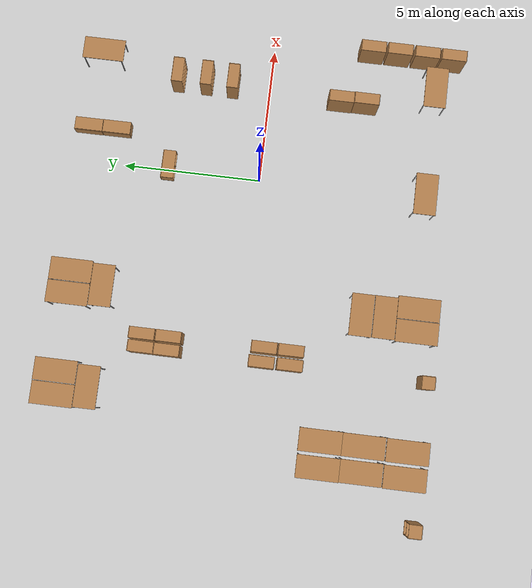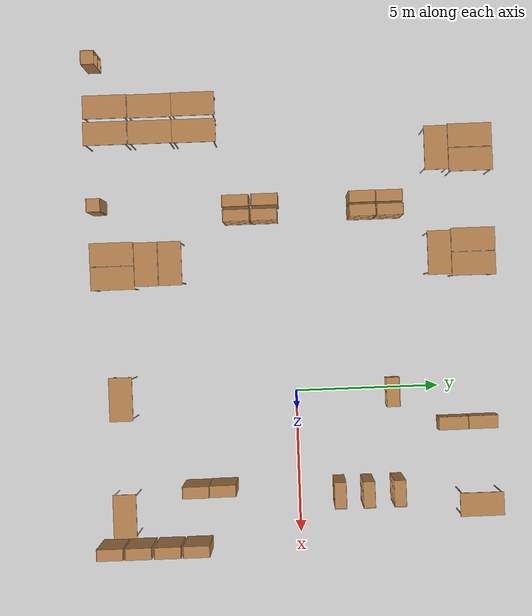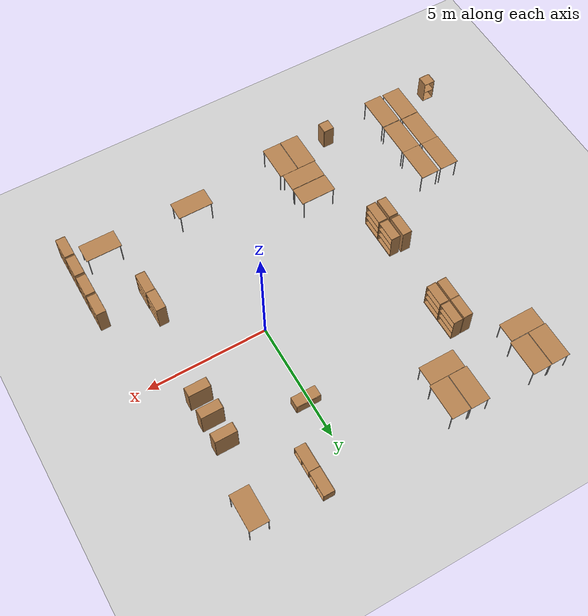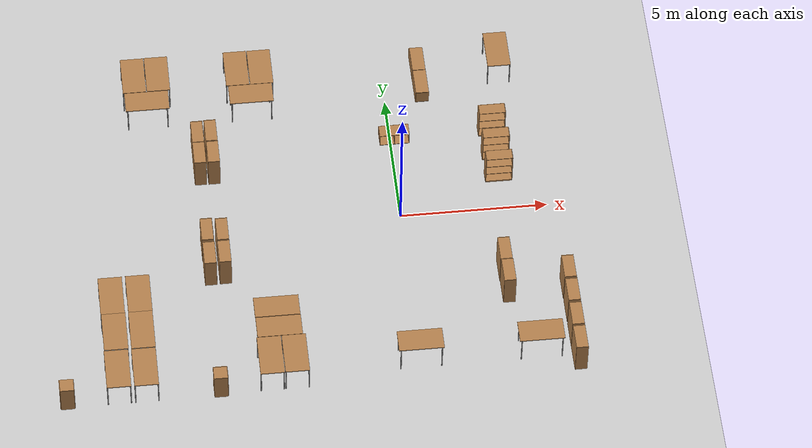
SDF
<sdf version="1.4">
 <world name="office">
  <physics type="ode">
   <real_time_update_rate>200</real_time_update_rate>
   <max_step_size>0.01</max_step_size>
   <real_time_factor>1</real_time_factor>
   <gravity>0 0 -9.8</gravity>
  </physics>
  <light name="sun" type="directional">
   <pose>0 0 10 0 -0 0</pose>
   <diffuse>0.8 0.8 0.8 1</diffuse>
   <specular>0.2 0.2 0.2 1</specular>
   <attenuation>
    <range>1000</range>
    <constant>0.9</constant>
    <linear>0.01</linear>
    <quadratic>0.001</quadratic>
   </attenuation>
   <direction>-0.5 0.1 -0.9</direction>
  </light>
  <model name="ground_plane">
   <static>1</static>
   <link name="link">
    <collision name="collision">
     <geometry><plane><normal>0 0 1</normal><size>100 100</size></plane></geometry>
     <surface><friction><ode><mu>100</mu><mu2>50</mu2></ode></friction></surface>
    </collision>
    <visual name="visual">
     <cast_shadows>0</cast_shadows>
     <geometry><plane><normal>0 0 1</normal><size>100 100</size></plane></geometry>
     <material>
      <script><uri>file://media/materials/scripts/gazebo.material</uri><name>Gazebo/Grey</name></script>
     </material>
    </visual>
    <velocity_decay><linear>0</linear><angular>0</angular></velocity_decay>
   </link>
  </model>
  <scene><ambient>0.4 0.4 0.4 1</ambient><background>0.7 0.7 0.7 1</background><shadows>1</shadows></scene>
  <model name="cabinet_3">
   <static>1</static>
   <link name="cabinet_bottom_plate">
    <inertial>
     <pose>0 0 -1 0 -0 0</pose>
     <inertia><ixx>2.05</ixx><ixy>0</ixy><ixz>0</ixz><iyy>2.05</iyy><iyz>0</iyz><izz>2.05</izz></inertia>
     <mass>25</mass>
    </inertial>
    <collision name="cabinet_bottom_plate_geom">
     <pose>0 0 0.01 0 -0 0</pose>
     <geometry><box><size>0.45 0.45 0.02</size></box></geometry>
    </collision>
    <visual name="cabinet_bottom_plate_geom_visual">
     <pose>0 0 0.01 0 -0 0</pose>
     <geometry><box><size>0.45 0.45 0.02</size></box></geometry>
     <material>
      <script><uri>file://media/materials/scripts/gazebo.material</uri><name>Gazebo/Wood</name></script>
     </material>
    </visual>
    <collision name="cabinet_bottom_plate_geom_cabinet_back_plate">
     <pose>0.235 0 0.51 0 -0 0</pose>
     <geometry><box><size>0.02 0.45 1.02</size></box></geometry>
    </collision>
    <visual name="cabinet_bottom_plate_geom_cabinet_back_plate_visual">
     <pose>0.235 0 0.51 0 -0 0</pose>
     <geometry><box><size>0.02 0.45 1.02</size></box></geometry>
     <material>
      <script><uri>file://media/materials/scripts/gazebo.material</uri><name>Gazebo/Wood</name></script>
     </material>
    </visual>
    <collision name="cabinet_bottom_plate_geom_cabinet_left_plate">
     <pose>0 0.235 0.51 0 -0 0</pose>
     <geometry><box><size>0.45 0.02 1.02</size></box></geometry>
    </collision>
    <visual name="cabinet_bottom_plate_geom_cabinet_left_plate_visual">
     <pose>0 0.235 0.51 0 -0 0</pose>
     <geometry><box><size>0.45 0.02 1.02</size></box></geometry>
     <material>
      <script><uri>file://media/materials/scripts/gazebo.material</uri><name>Gazebo/Wood</name></script>
     </material>
    </visual>
    <collision name="cabinet_bottom_plate_geom_cabinet_middle_plate">
     <pose>0 0 0.51 0 -0 0</pose>
     <geometry><box><size>0.45 0.45 0.02</size></box></geometry>
    </collision>
    <visual name="cabinet_bottom_plate_geom_cabinet_middle_plate_visual">
     <pose>0 0 0.51 0 -0 0</pose>
     <geometry><box><size>0.45 0.45 0.02</size></box></geometry>
     <material>
      <script><uri>file://media/materials/scripts/gazebo.material</uri><name>Gazebo/Wood</name></script>
     </material>
    </visual>
    <collision name="cabinet_bottom_plate_geom_cabinet_right_plate">
     <pose>0 -0.235 0.51 0 -0 0</pose>
     <geometry><box><size>0.45 0.02 1.02</size></box></geometry>
    </collision>
    <visual name="cabinet_bottom_plate_geom_cabinet_right_plate_visual">
     <pose>0 -0.235 0.51 0 -0 0</pose>
     <geometry><box><size>0.45 0.02 1.02</size></box></geometry>
     <material>
      <script><uri>file://media/materials/scripts/gazebo.material</uri><name>Gazebo/Wood</name></script>
     </material>
    </visual>
    <collision name="cabinet_bottom_plate_geom_cabinet_top_plate">
     <pose>0 0 1.01 0 -0 0</pose>
     <geometry><box><size>0.45 0.45 0.02</size></box></geometry>
    </collision>
    <visual name="cabinet_bottom_plate_geom_cabinet_top_plate_visual">
     <pose>0 0 1.01 0 -0 0</pose>
     <geometry><box><size>0.45 0.45 0.02</size></box></geometry>
     <material>
      <script><uri>file://media/materials/scripts/gazebo.material</uri><name>Gazebo/Wood</name></script>
     </material>
    </visual>
    <velocity_decay><linear>0</linear><angular>0</angular></velocity_decay>
   </link>
   <pose>-0.367518 3.35954 0.24 1.56 5.55112e-17 1.5708</pose>
  </model>
  <model name="bookshelf">
   <static>1</static>
   <link name="link">
    <inertial><mass>1</mass></inertial>
    <collision name="back">
     <pose>0 0.005 0.6 0 -0 0</pose>
     <geometry><box><size>0.9 0.01 1.2</size></box></geometry>
    </collision>
    <visual name="visual1">
     <pose>0 0.005 0.6 0 -0 0</pose>
     <geometry><box><size>0.9 0.01 1.2</size></box></geometry>
     <material>
      <script><uri>file://media/materials/scripts/gazebo.material</uri><name>Gazebo/Wood</name></script>
     </material>
    </visual>
    <collision name="left_side">
     <pose>0.45 -0.195 0.6 0 -0 0</pose>
     <geometry><box><size>0.02 0.4 1.2</size></box></geometry>
    </collision>
    <visual name="visual2">
     <pose>0.45 -0.195 0.6 0 -0 0</pose>
     <geometry><box><size>0.02 0.4 1.2</size></box></geometry>
     <material>
      <script><uri>file://media/materials/scripts/gazebo.material</uri><name>Gazebo/Wood</name></script>
     </material>
    </visual>
    <collision name="right_side">
     <pose>-0.45 -0.195 0.6 0 -0 0</pose>
     <geometry><box><size>0.02 0.4 1.2</size></box></geometry>
    </collision>
    <visual name="visual3">
     <pose>-0.45 -0.195 0.6 0 -0 0</pose>
     <geometry><box><size>0.02 0.4 1.2</size></box></geometry>
     <material>
      <script><uri>file://media/materials/scripts/gazebo.material</uri><name>Gazebo/Wood</name></script>
     </material>
    </visual>
    <collision name="bottom">
     <pose>0 -0.195 0.03 0 -0 0</pose>
     <geometry><box><size>0.88 0.4 0.06</size></box></geometry>
    </collision>
    <visual name="visual4">
     <pose>0 -0.195 0.03 0 -0 0</pose>
     <geometry><box><size>0.88 0.4 0.06</size></box></geometry>
     <material>
      <script><uri>file://media/materials/scripts/gazebo.material</uri><name>Gazebo/Wood</name></script>
     </material>
    </visual>
    <collision name="top">
     <pose>0 -0.195 1.19 0 -0 0</pose>
     <geometry><box><size>0.88 0.4 0.02</size></box></geometry>
    </collision>
    <visual name="visual5">
     <pose>0 -0.195 1.19 0 -0 0</pose>
     <geometry><box><size>0.88 0.4 0.02</size></box></geometry>
     <material>
      <script><uri>file://media/materials/scripts/gazebo.material</uri><name>Gazebo/Wood</name></script>
     </material>
    </visual>
    <collision name="low_shelf">
     <pose>0 -0.195 0.43 0 -0 0</pose>
     <geometry><box><size>0.88 0.4 0.02</size></box></geometry>
    </collision>
    <visual name="visual6">
     <pose>0 -0.195 0.43 0 -0 0</pose>
     <geometry><box><size>0.88 0.4 0.02</size></box></geometry>
     <material>
      <script><uri>file://media/materials/scripts/gazebo.material</uri><name>Gazebo/Wood</name></script>
     </material>
    </visual>
    <collision name="high_shelf">
     <pose>0 -0.195 0.8 0 -0 0</pose>
     <geometry><box><size>0.88 0.4 0.02</size></box></geometry>
    </collision>
    <visual name="visual7">
     <pose>0 -0.195 0.8 0 -0 0</pose>
     <geometry><box><size>0.88 0.4 0.02</size></box></geometry>
     <material>
      <script><uri>file://media/materials/scripts/gazebo.material</uri><name>Gazebo/Wood</name></script>
     </material>
    </visual>
    <velocity_decay><linear>0</linear><angular>0</angular></velocity_decay>
   </link>
   <pose>-6.31442 -0.893722 0 0 -0 1.5708</pose>
  </model>
  <model name="bookshelf_0">
   <static>1</static>
   <link name="link">
    <inertial><mass>1</mass></inertial>
    <collision name="back">
     <pose>0 0.005 0.6 0 -0 0</pose>
     <geometry><box><size>0.9 0.01 1.2</size></box></geometry>
    </collision>
    <visual name="visual1">
     <pose>0 0.005 0.6 0 -0 0</pose>
     <geometry><box><size>0.9 0.01 1.2</size></box></geometry>
     <material>
      <script><uri>file://media/materials/scripts/gazebo.material</uri><name>Gazebo/Wood</name></script>
     </material>
    </visual>
    <collision name="left_side">
     <pose>0.45 -0.195 0.6 0 -0 0</pose>
     <geometry><box><size>0.02 0.4 1.2</size></box></geometry>
    </collision>
    <visual name="visual2">
     <pose>0.45 -0.195 0.6 0 -0 0</pose>
     <geometry><box><size>0.02 0.4 1.2</size></box></geometry>
     <material>
      <script><uri>file://media/materials/scripts/gazebo.material</uri><name>Gazebo/Wood</name></script>
     </material>
    </visual>
    <collision name="right_side">
     <pose>-0.45 -0.195 0.6 0 -0 0</pose>
     <geometry><box><size>0.02 0.4 1.2</size></box></geometry>
    </collision>
    <visual name="visual3">
     <pose>-0.45 -0.195 0.6 0 -0 0</pose>
     <geometry><box><size>0.02 0.4 1.2</size></box></geometry>
     <material>
      <script><uri>file://media/materials/scripts/gazebo.material</uri><name>Gazebo/Wood</name></script>
     </material>
    </visual>
    <collision name="bottom">
     <pose>0 -0.195 0.03 0 -0 0</pose>
     <geometry><box><size>0.88 0.4 0.06</size></box></geometry>
    </collision>
    <visual name="visual4">
     <pose>0 -0.195 0.03 0 -0 0</pose>
     <geometry><box><size>0.88 0.4 0.06</size></box></geometry>
     <material>
      <script><uri>file://media/materials/scripts/gazebo.material</uri><name>Gazebo/Wood</name></script>
     </material>
    </visual>
    <collision name="top">
     <pose>0 -0.195 1.19 0 -0 0</pose>
     <geometry><box><size>0.88 0.4 0.02</size></box></geometry>
    </collision>
    <visual name="visual5">
     <pose>0 -0.195 1.19 0 -0 0</pose>
     <geometry><box><size>0.88 0.4 0.02</size></box></geometry>
     <material>
      <script><uri>file://media/materials/scripts/gazebo.material</uri><name>Gazebo/Wood</name></script>
     </material>
    </visual>
    <collision name="low_shelf">
     <pose>0 -0.195 0.43 0 -0 0</pose>
     <geometry><box><size>0.88 0.4 0.02</size></box></geometry>
    </collision>
    <visual name="visual6">
     <pose>0 -0.195 0.43 0 -0 0</pose>
     <geometry><box><size>0.88 0.4 0.02</size></box></geometry>
     <material>
      <script><uri>file://media/materials/scripts/gazebo.material</uri><name>Gazebo/Wood</name></script>
     </material>
    </visual>
    <collision name="high_shelf">
     <pose>0 -0.195 0.8 0 -0 0</pose>
     <geometry><box><size>0.88 0.4 0.02</size></box></geometry>
    </collision>
    <visual name="visual7">
     <pose>0 -0.195 0.8 0 -0 0</pose>
     <geometry><box><size>0.88 0.4 0.02</size></box></geometry>
     <material>
      <script><uri>file://media/materials/scripts/gazebo.material</uri><name>Gazebo/Wood</name></script>
     </material>
    </visual>
    <velocity_decay><linear>0</linear><angular>0</angular></velocity_decay>
   </link>
   <pose>-6.31523 -1.83923 0 0 -0 1.5708</pose>
  </model>
  <model name="bookshelf_1">
   <static>1</static>
   <link name="link">
    <inertial><mass>1</mass></inertial>
    <collision name="back">
     <pose>0 0.005 0.6 0 -0 0</pose>
     <geometry><box><size>0.9 0.01 1.2</size></box></geometry>
    </collision>
    <visual name="visual1">
     <pose>0 0.005 0.6 0 -0 0</pose>
     <geometry><box><size>0.9 0.01 1.2</size></box></geometry>
     <material>
      <script><uri>file://media/materials/scripts/gazebo.material</uri><name>Gazebo/Wood</name></script>
     </material>
    </visual>
    <collision name="left_side">
     <pose>0.45 -0.195 0.6 0 -0 0</pose>
     <geometry><box><size>0.02 0.4 1.2</size></box></geometry>
    </collision>
    <visual name="visual2">
     <pose>0.45 -0.195 0.6 0 -0 0</pose>
     <geometry><box><size>0.02 0.4 1.2</size></box></geometry>
     <material>
      <script><uri>file://media/materials/scripts/gazebo.material</uri><name>Gazebo/Wood</name></script>
     </material>
    </visual>
    <collision name="right_side">
     <pose>-0.45 -0.195 0.6 0 -0 0</pose>
     <geometry><box><size>0.02 0.4 1.2</size></box></geometry>
    </collision>
    <visual name="visual3">
     <pose>-0.45 -0.195 0.6 0 -0 0</pose>
     <geometry><box><size>0.02 0.4 1.2</size></box></geometry>
     <material>
      <script><uri>file://media/materials/scripts/gazebo.material</uri><name>Gazebo/Wood</name></script>
     </material>
    </visual>
    <collision name="bottom">
     <pose>0 -0.195 0.03 0 -0 0</pose>
     <geometry><box><size>0.88 0.4 0.06</size></box></geometry>
    </collision>
    <visual name="visual4">
     <pose>0 -0.195 0.03 0 -0 0</pose>
     <geometry><box><size>0.88 0.4 0.06</size></box></geometry>
     <material>
      <script><uri>file://media/materials/scripts/gazebo.material</uri><name>Gazebo/Wood</name></script>
     </material>
    </visual>
    <collision name="top">
     <pose>0 -0.195 1.19 0 -0 0</pose>
     <geometry><box><size>0.88 0.4 0.02</size></box></geometry>
    </collision>
    <visual name="visual5">
     <pose>0 -0.195 1.19 0 -0 0</pose>
     <geometry><box><size>0.88 0.4 0.02</size></box></geometry>
     <material>
      <script><uri>file://media/materials/scripts/gazebo.material</uri><name>Gazebo/Wood</name></script>
     </material>
    </visual>
    <collision name="low_shelf">
     <pose>0 -0.195 0.43 0 -0 0</pose>
     <geometry><box><size>0.88 0.4 0.02</size></box></geometry>
    </collision>
    <visual name="visual6">
     <pose>0 -0.195 0.43 0 -0 0</pose>
     <geometry><box><size>0.88 0.4 0.02</size></box></geometry>
     <material>
      <script><uri>file://media/materials/scripts/gazebo.material</uri><name>Gazebo/Wood</name></script>
     </material>
    </visual>
    <collision name="high_shelf">
     <pose>0 -0.195 0.8 0 -0 0</pose>
     <geometry><box><size>0.88 0.4 0.02</size></box></geometry>
    </collision>
    <visual name="visual7">
     <pose>0 -0.195 0.8 0 -0 0</pose>
     <geometry><box><size>0.88 0.4 0.02</size></box></geometry>
     <material>
      <script><uri>file://media/materials/scripts/gazebo.material</uri><name>Gazebo/Wood</name></script>
     </material>
    </visual>
    <velocity_decay><linear>0</linear><angular>0</angular></velocity_decay>
   </link>
   <pose>-6.43362 -0.854628 0 0 0 -1.5708</pose>
  </model>
  <model name="bookshelf_2">
   <static>1</static>
   <link name="link">
    <inertial><mass>1</mass></inertial>
    <collision name="back">
     <pose>0 0.005 0.6 0 -0 0</pose>
     <geometry><box><size>0.9 0.01 1.2</size></box></geometry>
    </collision>
    <visual name="visual1">
     <pose>0 0.005 0.6 0 -0 0</pose>
     <geometry><box><size>0.9 0.01 1.2</size></box></geometry>
     <material>
      <script><uri>file://media/materials/scripts/gazebo.material</uri><name>Gazebo/Wood</name></script>
     </material>
    </visual>
    <collision name="left_side">
     <pose>0.45 -0.195 0.6 0 -0 0</pose>
     <geometry><box><size>0.02 0.4 1.2</size></box></geometry>
    </collision>
    <visual name="visual2">
     <pose>0.45 -0.195 0.6 0 -0 0</pose>
     <geometry><box><size>0.02 0.4 1.2</size></box></geometry>
     <material>
      <script><uri>file://media/materials/scripts/gazebo.material</uri><name>Gazebo/Wood</name></script>
     </material>
    </visual>
    <collision name="right_side">
     <pose>-0.45 -0.195 0.6 0 -0 0</pose>
     <geometry><box><size>0.02 0.4 1.2</size></box></geometry>
    </collision>
    <visual name="visual3">
     <pose>-0.45 -0.195 0.6 0 -0 0</pose>
     <geometry><box><size>0.02 0.4 1.2</size></box></geometry>
     <material>
      <script><uri>file://media/materials/scripts/gazebo.material</uri><name>Gazebo/Wood</name></script>
     </material>
    </visual>
    <collision name="bottom">
     <pose>0 -0.195 0.03 0 -0 0</pose>
     <geometry><box><size>0.88 0.4 0.06</size></box></geometry>
    </collision>
    <visual name="visual4">
     <pose>0 -0.195 0.03 0 -0 0</pose>
     <geometry><box><size>0.88 0.4 0.06</size></box></geometry>
     <material>
      <script><uri>file://media/materials/scripts/gazebo.material</uri><name>Gazebo/Wood</name></script>
     </material>
    </visual>
    <collision name="top">
     <pose>0 -0.195 1.19 0 -0 0</pose>
     <geometry><box><size>0.88 0.4 0.02</size></box></geometry>
    </collision>
    <visual name="visual5">
     <pose>0 -0.195 1.19 0 -0 0</pose>
     <geometry><box><size>0.88 0.4 0.02</size></box></geometry>
     <material>
      <script><uri>file://media/materials/scripts/gazebo.material</uri><name>Gazebo/Wood</name></script>
     </material>
    </visual>
    <collision name="low_shelf">
     <pose>0 -0.195 0.43 0 -0 0</pose>
     <geometry><box><size>0.88 0.4 0.02</size></box></geometry>
    </collision>
    <visual name="visual6">
     <pose>0 -0.195 0.43 0 -0 0</pose>
     <geometry><box><size>0.88 0.4 0.02</size></box></geometry>
     <material>
      <script><uri>file://media/materials/scripts/gazebo.material</uri><name>Gazebo/Wood</name></script>
     </material>
    </visual>
    <collision name="high_shelf">
     <pose>0 -0.195 0.8 0 -0 0</pose>
     <geometry><box><size>0.88 0.4 0.02</size></box></geometry>
    </collision>
    <visual name="visual7">
     <pose>0 -0.195 0.8 0 -0 0</pose>
     <geometry><box><size>0.88 0.4 0.02</size></box></geometry>
     <material>
      <script><uri>file://media/materials/scripts/gazebo.material</uri><name>Gazebo/Wood</name></script>
     </material>
    </visual>
    <velocity_decay><linear>0</linear><angular>0</angular></velocity_decay>
   </link>
   <pose>-6.42598 -1.85096 0 0 0 -1.5708</pose>
  </model>
  <model name="cabinet_4">
   <static>1</static>
   <link name="cabinet_bottom_plate">
    <inertial>
     <pose>0 0 -1 0 -0 0</pose>
     <inertia><ixx>2.05</ixx><ixy>0</ixy><ixz>0</ixz><iyy>2.05</iyy><iyz>0</iyz><izz>2.05</izz></inertia>
     <mass>25</mass>
    </inertial>
    <collision name="cabinet_bottom_plate_geom">
     <pose>0 0 0.01 0 -0 0</pose>
     <geometry><box><size>0.45 0.45 0.02</size></box></geometry>
    </collision>
    <visual name="cabinet_bottom_plate_geom_visual">
     <pose>0 0 0.01 0 -0 0</pose>
     <geometry><box><size>0.45 0.45 0.02</size></box></geometry>
     <material>
      <script><uri>file://media/materials/scripts/gazebo.material</uri><name>Gazebo/Wood</name></script>
     </material>
    </visual>
    <collision name="cabinet_bottom_plate_geom_cabinet_back_plate">
     <pose>0.235 0 0.51 0 -0 0</pose>
     <geometry><box><size>0.02 0.45 1.02</size></box></geometry>
    </collision>
    <visual name="cabinet_bottom_plate_geom_cabinet_back_plate_visual">
     <pose>0.235 0 0.51 0 -0 0</pose>
     <geometry><box><size>0.02 0.45 1.02</size></box></geometry>
     <material>
      <script><uri>file://media/materials/scripts/gazebo.material</uri><name>Gazebo/Wood</name></script>
     </material>
    </visual>
    <collision name="cabinet_bottom_plate_geom_cabinet_left_plate">
     <pose>0 0.235 0.51 0 -0 0</pose>
     <geometry><box><size>0.45 0.02 1.02</size></box></geometry>
    </collision>
    <visual name="cabinet_bottom_plate_geom_cabinet_left_plate_visual">
     <pose>0 0.235 0.51 0 -0 0</pose>
     <geometry><box><size>0.45 0.02 1.02</size></box></geometry>
     <material>
      <script><uri>file://media/materials/scripts/gazebo.material</uri><name>Gazebo/Wood</name></script>
     </material>
    </visual>
    <collision name="cabinet_bottom_plate_geom_cabinet_middle_plate">
     <pose>0 0 0.51 0 -0 0</pose>
     <geometry><box><size>0.45 0.45 0.02</size></box></geometry>
    </collision>
    <visual name="cabinet_bottom_plate_geom_cabinet_middle_plate_visual">
     <pose>0 0 0.51 0 -0 0</pose>
     <geometry><box><size>0.45 0.45 0.02</size></box></geometry>
     <material>
      <script><uri>file://media/materials/scripts/gazebo.material</uri><name>Gazebo/Wood</name></script>
     </material>
    </visual>
    <collision name="cabinet_bottom_plate_geom_cabinet_right_plate">
     <pose>0 -0.235 0.51 0 -0 0</pose>
     <geometry><box><size>0.45 0.02 1.02</size></box></geometry>
    </collision>
    <visual name="cabinet_bottom_plate_geom_cabinet_right_plate_visual">
     <pose>0 -0.235 0.51 0 -0 0</pose>
     <geometry><box><size>0.45 0.02 1.02</size></box></geometry>
     <material>
      <script><uri>file://media/materials/scripts/gazebo.material</uri><name>Gazebo/Wood</name></script>
     </material>
    </visual>
    <collision name="cabinet_bottom_plate_geom_cabinet_top_plate">
     <pose>0 0 1.01 0 -0 0</pose>
     <geometry><box><size>0.45 0.45 0.02</size></box></geometry>
    </collision>
    <visual name="cabinet_bottom_plate_geom_cabinet_top_plate_visual">
     <pose>0 0 1.01 0 -0 0</pose>
     <geometry><box><size>0.45 0.45 0.02</size></box></geometry>
     <material>
      <script><uri>file://media/materials/scripts/gazebo.material</uri><name>Gazebo/Wood</name></script>
     </material>
    </visual>
    <velocity_decay><linear>0</linear><angular>0</angular></velocity_decay>
   </link>
   <pose>-11.7069 -6.71894 0 0 0 -1.5708</pose>
  </model>
  <model name="cabinet_5">
   <static>1</static>
   <link name="cabinet_bottom_plate">
    <inertial>
     <pose>0 0 -1 0 -0 0</pose>
     <inertia><ixx>2.05</ixx><ixy>0</ixy><ixz>0</ixz><iyy>2.05</iyy><iyz>0</iyz><izz>2.05</izz></inertia>
     <mass>25</mass>
    </inertial>
    <collision name="cabinet_bottom_plate_geom">
     <pose>0 0 0.01 0 -0 0</pose>
     <geometry><box><size>0.45 0.45 0.02</size></box></geometry>
    </collision>
    <visual name="cabinet_bottom_plate_geom_visual">
     <pose>0 0 0.01 0 -0 0</pose>
     <geometry><box><size>0.45 0.45 0.02</size></box></geometry>
     <material>
      <script><uri>file://media/materials/scripts/gazebo.material</uri><name>Gazebo/Wood</name></script>
     </material>
    </visual>
    <collision name="cabinet_bottom_plate_geom_cabinet_back_plate">
     <pose>0.235 0 0.51 0 -0 0</pose>
     <geometry><box><size>0.02 0.45 1.02</size></box></geometry>
    </collision>
    <visual name="cabinet_bottom_plate_geom_cabinet_back_plate_visual">
     <pose>0.235 0 0.51 0 -0 0</pose>
     <geometry><box><size>0.02 0.45 1.02</size></box></geometry>
     <material>
      <script><uri>file://media/materials/scripts/gazebo.material</uri><name>Gazebo/Wood</name></script>
     </material>
    </visual>
    <collision name="cabinet_bottom_plate_geom_cabinet_left_plate">
     <pose>0 0.235 0.51 0 -0 0</pose>
     <geometry><box><size>0.45 0.02 1.02</size></box></geometry>
    </collision>
    <visual name="cabinet_bottom_plate_geom_cabinet_left_plate_visual">
     <pose>0 0.235 0.51 0 -0 0</pose>
     <geometry><box><size>0.45 0.02 1.02</size></box></geometry>
     <material>
      <script><uri>file://media/materials/scripts/gazebo.material</uri><name>Gazebo/Wood</name></script>
     </material>
    </visual>
    <collision name="cabinet_bottom_plate_geom_cabinet_middle_plate">
     <pose>0 0 0.51 0 -0 0</pose>
     <geometry><box><size>0.45 0.45 0.02</size></box></geometry>
    </collision>
    <visual name="cabinet_bottom_plate_geom_cabinet_middle_plate_visual">
     <pose>0 0 0.51 0 -0 0</pose>
     <geometry><box><size>0.45 0.45 0.02</size></box></geometry>
     <material>
      <script><uri>file://media/materials/scripts/gazebo.material</uri><name>Gazebo/Wood</name></script>
     </material>
    </visual>
    <collision name="cabinet_bottom_plate_geom_cabinet_right_plate">
     <pose>0 -0.235 0.51 0 -0 0</pose>
     <geometry><box><size>0.45 0.02 1.02</size></box></geometry>
    </collision>
    <visual name="cabinet_bottom_plate_geom_cabinet_right_plate_visual">
     <pose>0 -0.235 0.51 0 -0 0</pose>
     <geometry><box><size>0.45 0.02 1.02</size></box></geometry>
     <material>
      <script><uri>file://media/materials/scripts/gazebo.material</uri><name>Gazebo/Wood</name></script>
     </material>
    </visual>
    <collision name="cabinet_bottom_plate_geom_cabinet_top_plate">
     <pose>0 0 1.01 0 -0 0</pose>
     <geometry><box><size>0.45 0.45 0.02</size></box></geometry>
    </collision>
    <visual name="cabinet_bottom_plate_geom_cabinet_top_plate_visual">
     <pose>0 0 1.01 0 -0 0</pose>
     <geometry><box><size>0.45 0.45 0.02</size></box></geometry>
     <material>
      <script><uri>file://media/materials/scripts/gazebo.material</uri><name>Gazebo/Wood</name></script>
     </material>
    </visual>
    <velocity_decay><linear>0</linear><angular>0</angular></velocity_decay>
   </link>
   <pose>-6.66649 -6.70658 0 0 -0 0</pose>
  </model>
  <model name="bookshelf_3">
   <static>1</static>
   <link name="link">
    <inertial><mass>1</mass></inertial>
    <collision name="back">
     <pose>0 0.005 0.6 0 -0 0</pose>
     <geometry><box><size>0.9 0.01 1.2</size></box></geometry>
    </collision>
    <visual name="visual1">
     <pose>0 0.005 0.6 0 -0 0</pose>
     <geometry><box><size>0.9 0.01 1.2</size></box></geometry>
     <material>
      <script><uri>file://media/materials/scripts/gazebo.material</uri><name>Gazebo/Wood</name></script>
     </material>
    </visual>
    <collision name="left_side">
     <pose>0.45 -0.195 0.6 0 -0 0</pose>
     <geometry><box><size>0.02 0.4 1.2</size></box></geometry>
    </collision>
    <visual name="visual2">
     <pose>0.45 -0.195 0.6 0 -0 0</pose>
     <geometry><box><size>0.02 0.4 1.2</size></box></geometry>
     <material>
      <script><uri>file://media/materials/scripts/gazebo.material</uri><name>Gazebo/Wood</name></script>
     </material>
    </visual>
    <collision name="right_side">
     <pose>-0.45 -0.195 0.6 0 -0 0</pose>
     <geometry><box><size>0.02 0.4 1.2</size></box></geometry>
    </collision>
    <visual name="visual3">
     <pose>-0.45 -0.195 0.6 0 -0 0</pose>
     <geometry><box><size>0.02 0.4 1.2</size></box></geometry>
     <material>
      <script><uri>file://media/materials/scripts/gazebo.material</uri><name>Gazebo/Wood</name></script>
     </material>
    </visual>
    <collision name="bottom">
     <pose>0 -0.195 0.03 0 -0 0</pose>
     <geometry><box><size>0.88 0.4 0.06</size></box></geometry>
    </collision>
    <visual name="visual4">
     <pose>0 -0.195 0.03 0 -0 0</pose>
     <geometry><box><size>0.88 0.4 0.06</size></box></geometry>
     <material>
      <script><uri>file://media/materials/scripts/gazebo.material</uri><name>Gazebo/Wood</name></script>
     </material>
    </visual>
    <collision name="top">
     <pose>0 -0.195 1.19 0 -0 0</pose>
     <geometry><box><size>0.88 0.4 0.02</size></box></geometry>
    </collision>
    <visual name="visual5">
     <pose>0 -0.195 1.19 0 -0 0</pose>
     <geometry><box><size>0.88 0.4 0.02</size></box></geometry>
     <material>
      <script><uri>file://media/materials/scripts/gazebo.material</uri><name>Gazebo/Wood</name></script>
     </material>
    </visual>
    <collision name="low_shelf">
     <pose>0 -0.195 0.43 0 -0 0</pose>
     <geometry><box><size>0.88 0.4 0.02</size></box></geometry>
    </collision>
    <visual name="visual6">
     <pose>0 -0.195 0.43 0 -0 0</pose>
     <geometry><box><size>0.88 0.4 0.02</size></box></geometry>
     <material>
      <script><uri>file://media/materials/scripts/gazebo.material</uri><name>Gazebo/Wood</name></script>
     </material>
    </visual>
    <collision name="high_shelf">
     <pose>0 -0.195 0.8 0 -0 0</pose>
     <geometry><box><size>0.88 0.4 0.02</size></box></geometry>
    </collision>
    <visual name="visual7">
     <pose>0 -0.195 0.8 0 -0 0</pose>
     <geometry><box><size>0.88 0.4 0.02</size></box></geometry>
     <material>
      <script><uri>file://media/materials/scripts/gazebo.material</uri><name>Gazebo/Wood</name></script>
     </material>
    </visual>
    <velocity_decay><linear>0</linear><angular>0</angular></velocity_decay>
   </link>
   <pose>3.02832 -3.53636 0 0 -0 1.5708</pose>
  </model>
  <model name="bookshelf_4">
   <static>1</static>
   <link name="link">
    <inertial><mass>1</mass></inertial>
    <collision name="back">
     <pose>0 0.005 0.6 0 -0 0</pose>
     <geometry><box><size>0.9 0.01 1.2</size></box></geometry>
    </collision>
    <visual name="visual1">
     <pose>0 0.005 0.6 0 -0 0</pose>
     <geometry><box><size>0.9 0.01 1.2</size></box></geometry>
     <material>
      <script><uri>file://media/materials/scripts/gazebo.material</uri><name>Gazebo/Wood</name></script>
     </material>
    </visual>
    <collision name="left_side">
     <pose>0.45 -0.195 0.6 0 -0 0</pose>
     <geometry><box><size>0.02 0.4 1.2</size></box></geometry>
    </collision>
    <visual name="visual2">
     <pose>0.45 -0.195 0.6 0 -0 0</pose>
     <geometry><box><size>0.02 0.4 1.2</size></box></geometry>
     <material>
      <script><uri>file://media/materials/scripts/gazebo.material</uri><name>Gazebo/Wood</name></script>
     </material>
    </visual>
    <collision name="right_side">
     <pose>-0.45 -0.195 0.6 0 -0 0</pose>
     <geometry><box><size>0.02 0.4 1.2</size></box></geometry>
    </collision>
    <visual name="visual3">
     <pose>-0.45 -0.195 0.6 0 -0 0</pose>
     <geometry><box><size>0.02 0.4 1.2</size></box></geometry>
     <material>
      <script><uri>file://media/materials/scripts/gazebo.material</uri><name>Gazebo/Wood</name></script>
     </material>
    </visual>
    <collision name="bottom">
     <pose>0 -0.195 0.03 0 -0 0</pose>
     <geometry><box><size>0.88 0.4 0.06</size></box></geometry>
    </collision>
    <visual name="visual4">
     <pose>0 -0.195 0.03 0 -0 0</pose>
     <geometry><box><size>0.88 0.4 0.06</size></box></geometry>
     <material>
      <script><uri>file://media/materials/scripts/gazebo.material</uri><name>Gazebo/Wood</name></script>
     </material>
    </visual>
    <collision name="top">
     <pose>0 -0.195 1.19 0 -0 0</pose>
     <geometry><box><size>0.88 0.4 0.02</size></box></geometry>
    </collision>
    <visual name="visual5">
     <pose>0 -0.195 1.19 0 -0 0</pose>
     <geometry><box><size>0.88 0.4 0.02</size></box></geometry>
     <material>
      <script><uri>file://media/materials/scripts/gazebo.material</uri><name>Gazebo/Wood</name></script>
     </material>
    </visual>
    <collision name="low_shelf">
     <pose>0 -0.195 0.43 0 -0 0</pose>
     <geometry><box><size>0.88 0.4 0.02</size></box></geometry>
    </collision>
    <visual name="visual6">
     <pose>0 -0.195 0.43 0 -0 0</pose>
     <geometry><box><size>0.88 0.4 0.02</size></box></geometry>
     <material>
      <script><uri>file://media/materials/scripts/gazebo.material</uri><name>Gazebo/Wood</name></script>
     </material>
    </visual>
    <collision name="high_shelf">
     <pose>0 -0.195 0.8 0 -0 0</pose>
     <geometry><box><size>0.88 0.4 0.02</size></box></geometry>
    </collision>
    <visual name="visual7">
     <pose>0 -0.195 0.8 0 -0 0</pose>
     <geometry><box><size>0.88 0.4 0.02</size></box></geometry>
     <material>
      <script><uri>file://media/materials/scripts/gazebo.material</uri><name>Gazebo/Wood</name></script>
     </material>
    </visual>
    <velocity_decay><linear>0</linear><angular>0</angular></velocity_decay>
   </link>
   <pose>3.01417 -2.62352 0 0 -0 1.5708</pose>
  </model>
  <model name="bookshelf_5">
   <static>1</static>
   <link name="link">
    <inertial><mass>1</mass></inertial>
    <collision name="back">
     <pose>0 0.005 0.6 0 -0 0</pose>
     <geometry><box><size>0.9 0.01 1.2</size></box></geometry>
    </collision>
    <visual name="visual1">
     <pose>0 0.005 0.6 0 -0 0</pose>
     <geometry><box><size>0.9 0.01 1.2</size></box></geometry>
     <material>
      <script><uri>file://media/materials/scripts/gazebo.material</uri><name>Gazebo/Wood</name></script>
     </material>
    </visual>
    <collision name="left_side">
     <pose>0.45 -0.195 0.6 0 -0 0</pose>
     <geometry><box><size>0.02 0.4 1.2</size></box></geometry>
    </collision>
    <visual name="visual2">
     <pose>0.45 -0.195 0.6 0 -0 0</pose>
     <geometry><box><size>0.02 0.4 1.2</size></box></geometry>
     <material>
      <script><uri>file://media/materials/scripts/gazebo.material</uri><name>Gazebo/Wood</name></script>
     </material>
    </visual>
    <collision name="right_side">
     <pose>-0.45 -0.195 0.6 0 -0 0</pose>
     <geometry><box><size>0.02 0.4 1.2</size></box></geometry>
    </collision>
    <visual name="visual3">
     <pose>-0.45 -0.195 0.6 0 -0 0</pose>
     <geometry><box><size>0.02 0.4 1.2</size></box></geometry>
     <material>
      <script><uri>file://media/materials/scripts/gazebo.material</uri><name>Gazebo/Wood</name></script>
     </material>
    </visual>
    <collision name="bottom">
     <pose>0 -0.195 0.03 0 -0 0</pose>
     <geometry><box><size>0.88 0.4 0.06</size></box></geometry>
    </collision>
    <visual name="visual4">
     <pose>0 -0.195 0.03 0 -0 0</pose>
     <geometry><box><size>0.88 0.4 0.06</size></box></geometry>
     <material>
      <script><uri>file://media/materials/scripts/gazebo.material</uri><name>Gazebo/Wood</name></script>
     </material>
    </visual>
    <collision name="top">
     <pose>0 -0.195 1.19 0 -0 0</pose>
     <geometry><box><size>0.88 0.4 0.02</size></box></geometry>
    </collision>
    <visual name="visual5">
     <pose>0 -0.195 1.19 0 -0 0</pose>
     <geometry><box><size>0.88 0.4 0.02</size></box></geometry>
     <material>
      <script><uri>file://media/materials/scripts/gazebo.material</uri><name>Gazebo/Wood</name></script>
     </material>
    </visual>
    <collision name="low_shelf">
     <pose>0 -0.195 0.43 0 -0 0</pose>
     <geometry><box><size>0.88 0.4 0.02</size></box></geometry>
    </collision>
    <visual name="visual6">
     <pose>0 -0.195 0.43 0 -0 0</pose>
     <geometry><box><size>0.88 0.4 0.02</size></box></geometry>
     <material>
      <script><uri>file://media/materials/scripts/gazebo.material</uri><name>Gazebo/Wood</name></script>
     </material>
    </visual>
    <collision name="high_shelf">
     <pose>0 -0.195 0.8 0 -0 0</pose>
     <geometry><box><size>0.88 0.4 0.02</size></box></geometry>
    </collision>
    <visual name="visual7">
     <pose>0 -0.195 0.8 0 -0 0</pose>
     <geometry><box><size>0.88 0.4 0.02</size></box></geometry>
     <material>
      <script><uri>file://media/materials/scripts/gazebo.material</uri><name>Gazebo/Wood</name></script>
     </material>
    </visual>
    <velocity_decay><linear>0</linear><angular>0</angular></velocity_decay>
   </link>
   <pose>-6.34031 2.45987 0 0 -0 1.5708</pose>
  </model>
  <model name="bookshelf_7">
   <static>1</static>
   <link name="link">
    <inertial><mass>1</mass></inertial>
    <collision name="back">
     <pose>0 0.005 0.6 0 -0 0</pose>
     <geometry><box><size>0.9 0.01 1.2</size></box></geometry>
    </collision>
    <visual name="visual1">
     <pose>0 0.005 0.6 0 -0 0</pose>
     <geometry><box><size>0.9 0.01 1.2</size></box></geometry>
     <material>
      <script><uri>file://media/materials/scripts/gazebo.material</uri><name>Gazebo/Wood</name></script>
     </material>
    </visual>
    <collision name="left_side">
     <pose>0.45 -0.195 0.6 0 -0 0</pose>
     <geometry><box><size>0.02 0.4 1.2</size></box></geometry>
    </collision>
    <visual name="visual2">
     <pose>0.45 -0.195 0.6 0 -0 0</pose>
     <geometry><box><size>0.02 0.4 1.2</size></box></geometry>
     <material>
      <script><uri>file://media/materials/scripts/gazebo.material</uri><name>Gazebo/Wood</name></script>
     </material>
    </visual>
    <collision name="right_side">
     <pose>-0.45 -0.195 0.6 0 -0 0</pose>
     <geometry><box><size>0.02 0.4 1.2</size></box></geometry>
    </collision>
    <visual name="visual3">
     <pose>-0.45 -0.195 0.6 0 -0 0</pose>
     <geometry><box><size>0.02 0.4 1.2</size></box></geometry>
     <material>
      <script><uri>file://media/materials/scripts/gazebo.material</uri><name>Gazebo/Wood</name></script>
     </material>
    </visual>
    <collision name="bottom">
     <pose>0 -0.195 0.03 0 -0 0</pose>
     <geometry><box><size>0.88 0.4 0.06</size></box></geometry>
    </collision>
    <visual name="visual4">
     <pose>0 -0.195 0.03 0 -0 0</pose>
     <geometry><box><size>0.88 0.4 0.06</size></box></geometry>
     <material>
      <script><uri>file://media/materials/scripts/gazebo.material</uri><name>Gazebo/Wood</name></script>
     </material>
    </visual>
    <collision name="top">
     <pose>0 -0.195 1.19 0 -0 0</pose>
     <geometry><box><size>0.88 0.4 0.02</size></box></geometry>
    </collision>
    <visual name="visual5">
     <pose>0 -0.195 1.19 0 -0 0</pose>
     <geometry><box><size>0.88 0.4 0.02</size></box></geometry>
     <material>
      <script><uri>file://media/materials/scripts/gazebo.material</uri><name>Gazebo/Wood</name></script>
     </material>
    </visual>
    <collision name="low_shelf">
     <pose>0 -0.195 0.43 0 -0 0</pose>
     <geometry><box><size>0.88 0.4 0.02</size></box></geometry>
    </collision>
    <visual name="visual6">
     <pose>0 -0.195 0.43 0 -0 0</pose>
     <geometry><box><size>0.88 0.4 0.02</size></box></geometry>
     <material>
      <script><uri>file://media/materials/scripts/gazebo.material</uri><name>Gazebo/Wood</name></script>
     </material>
    </visual>
    <collision name="high_shelf">
     <pose>0 -0.195 0.8 0 -0 0</pose>
     <geometry><box><size>0.88 0.4 0.02</size></box></geometry>
    </collision>
    <visual name="visual7">
     <pose>0 -0.195 0.8 0 -0 0</pose>
     <geometry><box><size>0.88 0.4 0.02</size></box></geometry>
     <material>
      <script><uri>file://media/materials/scripts/gazebo.material</uri><name>Gazebo/Wood</name></script>
     </material>
    </visual>
    <velocity_decay><linear>0</linear><angular>0</angular></velocity_decay>
   </link>
   <pose>-6.34296 3.39405 0 0 -0 1.5708</pose>
  </model>
  <model name="bookshelf_9">
   <static>1</static>
   <link name="link">
    <inertial><mass>1</mass></inertial>
    <collision name="back">
     <pose>0 0.005 0.6 0 -0 0</pose>
     <geometry><box><size>0.9 0.01 1.2</size></box></geometry>
    </collision>
    <visual name="visual1">
     <pose>0 0.005 0.6 0 -0 0</pose>
     <geometry><box><size>0.9 0.01 1.2</size></box></geometry>
     <material>
      <script><uri>file://media/materials/scripts/gazebo.material</uri><name>Gazebo/Wood</name></script>
     </material>
    </visual>
    <collision name="left_side">
     <pose>0.45 -0.195 0.6 0 -0 0</pose>
     <geometry><box><size>0.02 0.4 1.2</size></box></geometry>
    </collision>
    <visual name="visual2">
     <pose>0.45 -0.195 0.6 0 -0 0</pose>
     <geometry><box><size>0.02 0.4 1.2</size></box></geometry>
     <material>
      <script><uri>file://media/materials/scripts/gazebo.material</uri><name>Gazebo/Wood</name></script>
     </material>
    </visual>
    <collision name="right_side">
     <pose>-0.45 -0.195 0.6 0 -0 0</pose>
     <geometry><box><size>0.02 0.4 1.2</size></box></geometry>
    </collision>
    <visual name="visual3">
     <pose>-0.45 -0.195 0.6 0 -0 0</pose>
     <geometry><box><size>0.02 0.4 1.2</size></box></geometry>
     <material>
      <script><uri>file://media/materials/scripts/gazebo.material</uri><name>Gazebo/Wood</name></script>
     </material>
    </visual>
    <collision name="bottom">
     <pose>0 -0.195 0.03 0 -0 0</pose>
     <geometry><box><size>0.88 0.4 0.06</size></box></geometry>
    </collision>
    <visual name="visual4">
     <pose>0 -0.195 0.03 0 -0 0</pose>
     <geometry><box><size>0.88 0.4 0.06</size></box></geometry>
     <material>
      <script><uri>file://media/materials/scripts/gazebo.material</uri><name>Gazebo/Wood</name></script>
     </material>
    </visual>
    <collision name="top">
     <pose>0 -0.195 1.19 0 -0 0</pose>
     <geometry><box><size>0.88 0.4 0.02</size></box></geometry>
    </collision>
    <visual name="visual5">
     <pose>0 -0.195 1.19 0 -0 0</pose>
     <geometry><box><size>0.88 0.4 0.02</size></box></geometry>
     <material>
      <script><uri>file://media/materials/scripts/gazebo.material</uri><name>Gazebo/Wood</name></script>
     </material>
    </visual>
    <collision name="low_shelf">
     <pose>0 -0.195 0.43 0 -0 0</pose>
     <geometry><box><size>0.88 0.4 0.02</size></box></geometry>
    </collision>
    <visual name="visual6">
     <pose>0 -0.195 0.43 0 -0 0</pose>
     <geometry><box><size>0.88 0.4 0.02</size></box></geometry>
     <material>
      <script><uri>file://media/materials/scripts/gazebo.material</uri><name>Gazebo/Wood</name></script>
     </material>
    </visual>
    <collision name="high_shelf">
     <pose>0 -0.195 0.8 0 -0 0</pose>
     <geometry><box><size>0.88 0.4 0.02</size></box></geometry>
    </collision>
    <visual name="visual7">
     <pose>0 -0.195 0.8 0 -0 0</pose>
     <geometry><box><size>0.88 0.4 0.02</size></box></geometry>
     <material>
      <script><uri>file://media/materials/scripts/gazebo.material</uri><name>Gazebo/Wood</name></script>
     </material>
    </visual>
    <velocity_decay><linear>0</linear><angular>0</angular></velocity_decay>
   </link>
   <pose>3.50074 3.59039 0 0 -0 0</pose>
  </model>
  <model name="bookshelf_10">
   <static>1</static>
   <link name="link">
    <inertial><mass>1</mass></inertial>
    <collision name="back">
     <pose>0 0.005 0.6 0 -0 0</pose>
     <geometry><box><size>0.9 0.01 1.2</size></box></geometry>
    </collision>
    <visual name="visual1">
     <pose>0 0.005 0.6 0 -0 0</pose>
     <geometry><box><size>0.9 0.01 1.2</size></box></geometry>
     <material>
      <script><uri>file://media/materials/scripts/gazebo.material</uri><name>Gazebo/Wood</name></script>
     </material>
    </visual>
    <collision name="left_side">
     <pose>0.45 -0.195 0.6 0 -0 0</pose>
     <geometry><box><size>0.02 0.4 1.2</size></box></geometry>
    </collision>
    <visual name="visual2">
     <pose>0.45 -0.195 0.6 0 -0 0</pose>
     <geometry><box><size>0.02 0.4 1.2</size></box></geometry>
     <material>
      <script><uri>file://media/materials/scripts/gazebo.material</uri><name>Gazebo/Wood</name></script>
     </material>
    </visual>
    <collision name="right_side">
     <pose>-0.45 -0.195 0.6 0 -0 0</pose>
     <geometry><box><size>0.02 0.4 1.2</size></box></geometry>
    </collision>
    <visual name="visual3">
     <pose>-0.45 -0.195 0.6 0 -0 0</pose>
     <geometry><box><size>0.02 0.4 1.2</size></box></geometry>
     <material>
      <script><uri>file://media/materials/scripts/gazebo.material</uri><name>Gazebo/Wood</name></script>
     </material>
    </visual>
    <collision name="bottom">
     <pose>0 -0.195 0.03 0 -0 0</pose>
     <geometry><box><size>0.88 0.4 0.06</size></box></geometry>
    </collision>
    <visual name="visual4">
     <pose>0 -0.195 0.03 0 -0 0</pose>
     <geometry><box><size>0.88 0.4 0.06</size></box></geometry>
     <material>
      <script><uri>file://media/materials/scripts/gazebo.material</uri><name>Gazebo/Wood</name></script>
     </material>
    </visual>
    <collision name="top">
     <pose>0 -0.195 1.19 0 -0 0</pose>
     <geometry><box><size>0.88 0.4 0.02</size></box></geometry>
    </collision>
    <visual name="visual5">
     <pose>0 -0.195 1.19 0 -0 0</pose>
     <geometry><box><size>0.88 0.4 0.02</size></box></geometry>
     <material>
      <script><uri>file://media/materials/scripts/gazebo.material</uri><name>Gazebo/Wood</name></script>
     </material>
    </visual>
    <collision name="low_shelf">
     <pose>0 -0.195 0.43 0 -0 0</pose>
     <geometry><box><size>0.88 0.4 0.02</size></box></geometry>
    </collision>
    <visual name="visual6">
     <pose>0 -0.195 0.43 0 -0 0</pose>
     <geometry><box><size>0.88 0.4 0.02</size></box></geometry>
     <material>
      <script><uri>file://media/materials/scripts/gazebo.material</uri><name>Gazebo/Wood</name></script>
     </material>
    </visual>
    <collision name="high_shelf">
     <pose>0 -0.195 0.8 0 -0 0</pose>
     <geometry><box><size>0.88 0.4 0.02</size></box></geometry>
    </collision>
    <visual name="visual7">
     <pose>0 -0.195 0.8 0 -0 0</pose>
     <geometry><box><size>0.88 0.4 0.02</size></box></geometry>
     <material>
      <script><uri>file://media/materials/scripts/gazebo.material</uri><name>Gazebo/Wood</name></script>
     </material>
    </visual>
    <velocity_decay><linear>0</linear><angular>0</angular></velocity_decay>
   </link>
   <pose>3.50768 2.53773 0 0 -0 0</pose>
  </model>
  <model name="bookshelf_11">
   <static>1</static>
   <link name="link">
    <inertial><mass>1</mass></inertial>
    <collision name="back">
     <pose>0 0.005 0.6 0 -0 0</pose>
     <geometry><box><size>0.9 0.01 1.2</size></box></geometry>
    </collision>
    <visual name="visual1">
     <pose>0 0.005 0.6 0 -0 0</pose>
     <geometry><box><size>0.9 0.01 1.2</size></box></geometry>
     <material>
      <script><uri>file://media/materials/scripts/gazebo.material</uri><name>Gazebo/Wood</name></script>
     </material>
    </visual>
    <collision name="left_side">
     <pose>0.45 -0.195 0.6 0 -0 0</pose>
     <geometry><box><size>0.02 0.4 1.2</size></box></geometry>
    </collision>
    <visual name="visual2">
     <pose>0.45 -0.195 0.6 0 -0 0</pose>
     <geometry><box><size>0.02 0.4 1.2</size></box></geometry>
     <material>
      <script><uri>file://media/materials/scripts/gazebo.material</uri><name>Gazebo/Wood</name></script>
     </material>
    </visual>
    <collision name="right_side">
     <pose>-0.45 -0.195 0.6 0 -0 0</pose>
     <geometry><box><size>0.02 0.4 1.2</size></box></geometry>
    </collision>
    <visual name="visual3">
     <pose>-0.45 -0.195 0.6 0 -0 0</pose>
     <geometry><box><size>0.02 0.4 1.2</size></box></geometry>
     <material>
      <script><uri>file://media/materials/scripts/gazebo.material</uri><name>Gazebo/Wood</name></script>
     </material>
    </visual>
    <collision name="bottom">
     <pose>0 -0.195 0.03 0 -0 0</pose>
     <geometry><box><size>0.88 0.4 0.06</size></box></geometry>
    </collision>
    <visual name="visual4">
     <pose>0 -0.195 0.03 0 -0 0</pose>
     <geometry><box><size>0.88 0.4 0.06</size></box></geometry>
     <material>
      <script><uri>file://media/materials/scripts/gazebo.material</uri><name>Gazebo/Wood</name></script>
     </material>
    </visual>
    <collision name="top">
     <pose>0 -0.195 1.19 0 -0 0</pose>
     <geometry><box><size>0.88 0.4 0.02</size></box></geometry>
    </collision>
    <visual name="visual5">
     <pose>0 -0.195 1.19 0 -0 0</pose>
     <geometry><box><size>0.88 0.4 0.02</size></box></geometry>
     <material>
      <script><uri>file://media/materials/scripts/gazebo.material</uri><name>Gazebo/Wood</name></script>
     </material>
    </visual>
    <collision name="low_shelf">
     <pose>0 -0.195 0.43 0 -0 0</pose>
     <geometry><box><size>0.88 0.4 0.02</size></box></geometry>
    </collision>
    <visual name="visual6">
     <pose>0 -0.195 0.43 0 -0 0</pose>
     <geometry><box><size>0.88 0.4 0.02</size></box></geometry>
     <material>
      <script><uri>file://media/materials/scripts/gazebo.material</uri><name>Gazebo/Wood</name></script>
     </material>
    </visual>
    <collision name="high_shelf">
     <pose>0 -0.195 0.8 0 -0 0</pose>
     <geometry><box><size>0.88 0.4 0.02</size></box></geometry>
    </collision>
    <visual name="visual7">
     <pose>0 -0.195 0.8 0 -0 0</pose>
     <geometry><box><size>0.88 0.4 0.02</size></box></geometry>
     <material>
      <script><uri>file://media/materials/scripts/gazebo.material</uri><name>Gazebo/Wood</name></script>
     </material>
    </visual>
    <velocity_decay><linear>0</linear><angular>0</angular></velocity_decay>
   </link>
   <pose>3.49876 1.56425 0 0 -0 0</pose>
  </model>
  <model name="cabinet_6">
   <static>1</static>
   <link name="cabinet_bottom_plate">
    <inertial>
     <pose>0 0 -1 0 -0 0</pose>
     <inertia><ixx>2.05</ixx><ixy>0</ixy><ixz>0</ixz><iyy>2.05</iyy><iyz>0</iyz><izz>2.05</izz></inertia>
     <mass>25</mass>
    </inertial>
    <collision name="cabinet_bottom_plate_geom">
     <pose>0 0 0.01 0 -0 0</pose>
     <geometry><box><size>0.45 0.45 0.02</size></box></geometry>
    </collision>
    <visual name="cabinet_bottom_plate_geom_visual">
     <pose>0 0 0.01 0 -0 0</pose>
     <geometry><box><size>0.45 0.45 0.02</size></box></geometry>
     <material>
      <script><uri>file://media/materials/scripts/gazebo.material</uri><name>Gazebo/Wood</name></script>
     </material>
    </visual>
    <collision name="cabinet_bottom_plate_geom_cabinet_back_plate">
     <pose>0.235 0 0.51 0 -0 0</pose>
     <geometry><box><size>0.02 0.45 1.02</size></box></geometry>
    </collision>
    <visual name="cabinet_bottom_plate_geom_cabinet_back_plate_visual">
     <pose>0.235 0 0.51 0 -0 0</pose>
     <geometry><box><size>0.02 0.45 1.02</size></box></geometry>
     <material>
      <script><uri>file://media/materials/scripts/gazebo.material</uri><name>Gazebo/Wood</name></script>
     </material>
    </visual>
    <collision name="cabinet_bottom_plate_geom_cabinet_left_plate">
     <pose>0 0.235 0.51 0 -0 0</pose>
     <geometry><box><size>0.45 0.02 1.02</size></box></geometry>
    </collision>
    <visual name="cabinet_bottom_plate_geom_cabinet_left_plate_visual">
     <pose>0 0.235 0.51 0 -0 0</pose>
     <geometry><box><size>0.45 0.02 1.02</size></box></geometry>
     <material>
      <script><uri>file://media/materials/scripts/gazebo.material</uri><name>Gazebo/Wood</name></script>
     </material>
    </visual>
    <collision name="cabinet_bottom_plate_geom_cabinet_middle_plate">
     <pose>0 0 0.51 0 -0 0</pose>
     <geometry><box><size>0.45 0.45 0.02</size></box></geometry>
    </collision>
    <visual name="cabinet_bottom_plate_geom_cabinet_middle_plate_visual">
     <pose>0 0 0.51 0 -0 0</pose>
     <geometry><box><size>0.45 0.45 0.02</size></box></geometry>
     <material>
      <script><uri>file://media/materials/scripts/gazebo.material</uri><name>Gazebo/Wood</name></script>
     </material>
    </visual>
    <collision name="cabinet_bottom_plate_geom_cabinet_right_plate">
     <pose>0 -0.235 0.51 0 -0 0</pose>
     <geometry><box><size>0.45 0.02 1.02</size></box></geometry>
    </collision>
    <visual name="cabinet_bottom_plate_geom_cabinet_right_plate_visual">
     <pose>0 -0.235 0.51 0 -0 0</pose>
     <geometry><box><size>0.45 0.02 1.02</size></box></geometry>
     <material>
      <script><uri>file://media/materials/scripts/gazebo.material</uri><name>Gazebo/Wood</name></script>
     </material>
    </visual>
    <collision name="cabinet_bottom_plate_geom_cabinet_top_plate">
     <pose>0 0 1.01 0 -0 0</pose>
     <geometry><box><size>0.45 0.45 0.02</size></box></geometry>
    </collision>
    <visual name="cabinet_bottom_plate_geom_cabinet_top_plate_visual">
     <pose>0 0 1.01 0 -0 0</pose>
     <geometry><box><size>0.45 0.45 0.02</size></box></geometry>
     <material>
      <script><uri>file://media/materials/scripts/gazebo.material</uri><name>Gazebo/Wood</name></script>
     </material>
    </visual>
    <velocity_decay><linear>0</linear><angular>0</angular></velocity_decay>
   </link>
   <pose>1.29334 5.93491 0.26 -1.56 4.23516e-22 -3.14159</pose>
  </model>
  <model name="cabinet_7">
   <static>1</static>
   <link name="cabinet_bottom_plate">
    <inertial>
     <pose>0 0 -1 0 -0 0</pose>
     <inertia><ixx>2.05</ixx><ixy>0</ixy><ixz>0</ixz><iyy>2.05</iyy><iyz>0</iyz><izz>2.05</izz></inertia>
     <mass>25</mass>
    </inertial>
    <collision name="cabinet_bottom_plate_geom">
     <pose>0 0 0.01 0 -0 0</pose>
     <geometry><box><size>0.45 0.45 0.02</size></box></geometry>
    </collision>
    <visual name="cabinet_bottom_plate_geom_visual">
     <pose>0 0 0.01 0 -0 0</pose>
     <geometry><box><size>0.45 0.45 0.02</size></box></geometry>
     <material>
      <script><uri>file://media/materials/scripts/gazebo.material</uri><name>Gazebo/Wood</name></script>
     </material>
    </visual>
    <collision name="cabinet_bottom_plate_geom_cabinet_back_plate">
     <pose>0.235 0 0.51 0 -0 0</pose>
     <geometry><box><size>0.02 0.45 1.02</size></box></geometry>
    </collision>
    <visual name="cabinet_bottom_plate_geom_cabinet_back_plate_visual">
     <pose>0.235 0 0.51 0 -0 0</pose>
     <geometry><box><size>0.02 0.45 1.02</size></box></geometry>
     <material>
      <script><uri>file://media/materials/scripts/gazebo.material</uri><name>Gazebo/Wood</name></script>
     </material>
    </visual>
    <collision name="cabinet_bottom_plate_geom_cabinet_left_plate">
     <pose>0 0.235 0.51 0 -0 0</pose>
     <geometry><box><size>0.45 0.02 1.02</size></box></geometry>
    </collision>
    <visual name="cabinet_bottom_plate_geom_cabinet_left_plate_visual">
     <pose>0 0.235 0.51 0 -0 0</pose>
     <geometry><box><size>0.45 0.02 1.02</size></box></geometry>
     <material>
      <script><uri>file://media/materials/scripts/gazebo.material</uri><name>Gazebo/Wood</name></script>
     </material>
    </visual>
    <collision name="cabinet_bottom_plate_geom_cabinet_middle_plate">
     <pose>0 0 0.51 0 -0 0</pose>
     <geometry><box><size>0.45 0.45 0.02</size></box></geometry>
    </collision>
    <visual name="cabinet_bottom_plate_geom_cabinet_middle_plate_visual">
     <pose>0 0 0.51 0 -0 0</pose>
     <geometry><box><size>0.45 0.45 0.02</size></box></geometry>
     <material>
      <script><uri>file://media/materials/scripts/gazebo.material</uri><name>Gazebo/Wood</name></script>
     </material>
    </visual>
    <collision name="cabinet_bottom_plate_geom_cabinet_right_plate">
     <pose>0 -0.235 0.51 0 -0 0</pose>
     <geometry><box><size>0.45 0.02 1.02</size></box></geometry>
    </collision>
    <visual name="cabinet_bottom_plate_geom_cabinet_right_plate_visual">
     <pose>0 -0.235 0.51 0 -0 0</pose>
     <geometry><box><size>0.45 0.02 1.02</size></box></geometry>
     <material>
      <script><uri>file://media/materials/scripts/gazebo.material</uri><name>Gazebo/Wood</name></script>
     </material>
    </visual>
    <collision name="cabinet_bottom_plate_geom_cabinet_top_plate">
     <pose>0 0 1.01 0 -0 0</pose>
     <geometry><box><size>0.45 0.45 0.02</size></box></geometry>
    </collision>
    <visual name="cabinet_bottom_plate_geom_cabinet_top_plate_visual">
     <pose>0 0 1.01 0 -0 0</pose>
     <geometry><box><size>0.45 0.45 0.02</size></box></geometry>
     <material>
      <script><uri>file://media/materials/scripts/gazebo.material</uri><name>Gazebo/Wood</name></script>
     </material>
    </visual>
    <velocity_decay><linear>0</linear><angular>0</angular></velocity_decay>
   </link>
   <pose>1.28862 6.97136 0.25 -1.56 4.23516e-22 -3.14159</pose>
  </model>
  <model name="bookshelf_12">
   <static>1</static>
   <link name="link">
    <inertial><mass>1</mass></inertial>
    <collision name="back">
     <pose>0 0.005 0.6 0 -0 0</pose>
     <geometry><box><size>0.9 0.01 1.2</size></box></geometry>
    </collision>
    <visual name="visual1">
     <pose>0 0.005 0.6 0 -0 0</pose>
     <geometry><box><size>0.9 0.01 1.2</size></box></geometry>
     <material>
      <script><uri>file://media/materials/scripts/gazebo.material</uri><name>Gazebo/Wood</name></script>
     </material>
    </visual>
    <collision name="left_side">
     <pose>0.45 -0.195 0.6 0 -0 0</pose>
     <geometry><box><size>0.02 0.4 1.2</size></box></geometry>
    </collision>
    <visual name="visual2">
     <pose>0.45 -0.195 0.6 0 -0 0</pose>
     <geometry><box><size>0.02 0.4 1.2</size></box></geometry>
     <material>
      <script><uri>file://media/materials/scripts/gazebo.material</uri><name>Gazebo/Wood</name></script>
     </material>
    </visual>
    <collision name="right_side">
     <pose>-0.45 -0.195 0.6 0 -0 0</pose>
     <geometry><box><size>0.02 0.4 1.2</size></box></geometry>
    </collision>
    <visual name="visual3">
     <pose>-0.45 -0.195 0.6 0 -0 0</pose>
     <geometry><box><size>0.02 0.4 1.2</size></box></geometry>
     <material>
      <script><uri>file://media/materials/scripts/gazebo.material</uri><name>Gazebo/Wood</name></script>
     </material>
    </visual>
    <collision name="bottom">
     <pose>0 -0.195 0.03 0 -0 0</pose>
     <geometry><box><size>0.88 0.4 0.06</size></box></geometry>
    </collision>
    <visual name="visual4">
     <pose>0 -0.195 0.03 0 -0 0</pose>
     <geometry><box><size>0.88 0.4 0.06</size></box></geometry>
     <material>
      <script><uri>file://media/materials/scripts/gazebo.material</uri><name>Gazebo/Wood</name></script>
     </material>
    </visual>
    <collision name="top">
     <pose>0 -0.195 1.19 0 -0 0</pose>
     <geometry><box><size>0.88 0.4 0.02</size></box></geometry>
    </collision>
    <visual name="visual5">
     <pose>0 -0.195 1.19 0 -0 0</pose>
     <geometry><box><size>0.88 0.4 0.02</size></box></geometry>
     <material>
      <script><uri>file://media/materials/scripts/gazebo.material</uri><name>Gazebo/Wood</name></script>
     </material>
    </visual>
    <collision name="low_shelf">
     <pose>0 -0.195 0.43 0 -0 0</pose>
     <geometry><box><size>0.88 0.4 0.02</size></box></geometry>
    </collision>
    <visual name="visual6">
     <pose>0 -0.195 0.43 0 -0 0</pose>
     <geometry><box><size>0.88 0.4 0.02</size></box></geometry>
     <material>
      <script><uri>file://media/materials/scripts/gazebo.material</uri><name>Gazebo/Wood</name></script>
     </material>
    </visual>
    <collision name="high_shelf">
     <pose>0 -0.195 0.8 0 -0 0</pose>
     <geometry><box><size>0.88 0.4 0.02</size></box></geometry>
    </collision>
    <visual name="visual7">
     <pose>0 -0.195 0.8 0 -0 0</pose>
     <geometry><box><size>0.88 0.4 0.02</size></box></geometry>
     <material>
      <script><uri>file://media/materials/scripts/gazebo.material</uri><name>Gazebo/Wood</name></script>
     </material>
    </visual>
    <velocity_decay><linear>0</linear><angular>0</angular></velocity_decay>
   </link>
   <pose>-6.41767 2.4645 0 0 0 -1.5708</pose>
  </model>
  <model name="bookshelf_13">
   <static>1</static>
   <link name="link">
    <inertial><mass>1</mass></inertial>
    <collision name="back">
     <pose>0 0.005 0.6 0 -0 0</pose>
     <geometry><box><size>0.9 0.01 1.2</size></box></geometry>
    </collision>
    <visual name="visual1">
     <pose>0 0.005 0.6 0 -0 0</pose>
     <geometry><box><size>0.9 0.01 1.2</size></box></geometry>
     <material>
      <script><uri>file://media/materials/scripts/gazebo.material</uri><name>Gazebo/Wood</name></script>
     </material>
    </visual>
    <collision name="left_side">
     <pose>0.45 -0.195 0.6 0 -0 0</pose>
     <geometry><box><size>0.02 0.4 1.2</size></box></geometry>
    </collision>
    <visual name="visual2">
     <pose>0.45 -0.195 0.6 0 -0 0</pose>
     <geometry><box><size>0.02 0.4 1.2</size></box></geometry>
     <material>
      <script><uri>file://media/materials/scripts/gazebo.material</uri><name>Gazebo/Wood</name></script>
     </material>
    </visual>
    <collision name="right_side">
     <pose>-0.45 -0.195 0.6 0 -0 0</pose>
     <geometry><box><size>0.02 0.4 1.2</size></box></geometry>
    </collision>
    <visual name="visual3">
     <pose>-0.45 -0.195 0.6 0 -0 0</pose>
     <geometry><box><size>0.02 0.4 1.2</size></box></geometry>
     <material>
      <script><uri>file://media/materials/scripts/gazebo.material</uri><name>Gazebo/Wood</name></script>
     </material>
    </visual>
    <collision name="bottom">
     <pose>0 -0.195 0.03 0 -0 0</pose>
     <geometry><box><size>0.88 0.4 0.06</size></box></geometry>
    </collision>
    <visual name="visual4">
     <pose>0 -0.195 0.03 0 -0 0</pose>
     <geometry><box><size>0.88 0.4 0.06</size></box></geometry>
     <material>
      <script><uri>file://media/materials/scripts/gazebo.material</uri><name>Gazebo/Wood</name></script>
     </material>
    </visual>
    <collision name="top">
     <pose>0 -0.195 1.19 0 -0 0</pose>
     <geometry><box><size>0.88 0.4 0.02</size></box></geometry>
    </collision>
    <visual name="visual5">
     <pose>0 -0.195 1.19 0 -0 0</pose>
     <geometry><box><size>0.88 0.4 0.02</size></box></geometry>
     <material>
      <script><uri>file://media/materials/scripts/gazebo.material</uri><name>Gazebo/Wood</name></script>
     </material>
    </visual>
    <collision name="low_shelf">
     <pose>0 -0.195 0.43 0 -0 0</pose>
     <geometry><box><size>0.88 0.4 0.02</size></box></geometry>
    </collision>
    <visual name="visual6">
     <pose>0 -0.195 0.43 0 -0 0</pose>
     <geometry><box><size>0.88 0.4 0.02</size></box></geometry>
     <material>
      <script><uri>file://media/materials/scripts/gazebo.material</uri><name>Gazebo/Wood</name></script>
     </material>
    </visual>
    <collision name="high_shelf">
     <pose>0 -0.195 0.8 0 -0 0</pose>
     <geometry><box><size>0.88 0.4 0.02</size></box></geometry>
    </collision>
    <visual name="visual7">
     <pose>0 -0.195 0.8 0 -0 0</pose>
     <geometry><box><size>0.88 0.4 0.02</size></box></geometry>
     <material>
      <script><uri>file://media/materials/scripts/gazebo.material</uri><name>Gazebo/Wood</name></script>
     </material>
    </visual>
    <velocity_decay><linear>0</linear><angular>0</angular></velocity_decay>
   </link>
   <pose>-6.41358 3.37736 0 0 0 -1.5708</pose>
  </model>
  <model name="bookshelf_15">
   <static>1</static>
   <link name="link">
    <inertial><mass>1</mass></inertial>
    <collision name="back">
     <pose>0 0.005 0.6 0 -0 0</pose>
     <geometry><box><size>0.9 0.01 1.2</size></box></geometry>
    </collision>
    <visual name="visual1">
     <pose>0 0.005 0.6 0 -0 0</pose>
     <geometry><box><size>0.9 0.01 1.2</size></box></geometry>
     <material>
      <script><uri>file://media/materials/scripts/gazebo.material</uri><name>Gazebo/Wood</name></script>
     </material>
    </visual>
    <collision name="left_side">
     <pose>0.45 -0.195 0.6 0 -0 0</pose>
     <geometry><box><size>0.02 0.4 1.2</size></box></geometry>
    </collision>
    <visual name="visual2">
     <pose>0.45 -0.195 0.6 0 -0 0</pose>
     <geometry><box><size>0.02 0.4 1.2</size></box></geometry>
     <material>
      <script><uri>file://media/materials/scripts/gazebo.material</uri><name>Gazebo/Wood</name></script>
     </material>
    </visual>
    <collision name="right_side">
     <pose>-0.45 -0.195 0.6 0 -0 0</pose>
     <geometry><box><size>0.02 0.4 1.2</size></box></geometry>
    </collision>
    <visual name="visual3">
     <pose>-0.45 -0.195 0.6 0 -0 0</pose>
     <geometry><box><size>0.02 0.4 1.2</size></box></geometry>
     <material>
      <script><uri>file://media/materials/scripts/gazebo.material</uri><name>Gazebo/Wood</name></script>
     </material>
    </visual>
    <collision name="bottom">
     <pose>0 -0.195 0.03 0 -0 0</pose>
     <geometry><box><size>0.88 0.4 0.06</size></box></geometry>
    </collision>
    <visual name="visual4">
     <pose>0 -0.195 0.03 0 -0 0</pose>
     <geometry><box><size>0.88 0.4 0.06</size></box></geometry>
     <material>
      <script><uri>file://media/materials/scripts/gazebo.material</uri><name>Gazebo/Wood</name></script>
     </material>
    </visual>
    <collision name="top">
     <pose>0 -0.195 1.19 0 -0 0</pose>
     <geometry><box><size>0.88 0.4 0.02</size></box></geometry>
    </collision>
    <visual name="visual5">
     <pose>0 -0.195 1.19 0 -0 0</pose>
     <geometry><box><size>0.88 0.4 0.02</size></box></geometry>
     <material>
      <script><uri>file://media/materials/scripts/gazebo.material</uri><name>Gazebo/Wood</name></script>
     </material>
    </visual>
    <collision name="low_shelf">
     <pose>0 -0.195 0.43 0 -0 0</pose>
     <geometry><box><size>0.88 0.4 0.02</size></box></geometry>
    </collision>
    <visual name="visual6">
     <pose>0 -0.195 0.43 0 -0 0</pose>
     <geometry><box><size>0.88 0.4 0.02</size></box></geometry>
     <material>
      <script><uri>file://media/materials/scripts/gazebo.material</uri><name>Gazebo/Wood</name></script>
     </material>
    </visual>
    <collision name="high_shelf">
     <pose>0 -0.195 0.8 0 -0 0</pose>
     <geometry><box><size>0.88 0.4 0.02</size></box></geometry>
    </collision>
    <visual name="visual7">
     <pose>0 -0.195 0.8 0 -0 0</pose>
     <geometry><box><size>0.88 0.4 0.02</size></box></geometry>
     <material>
      <script><uri>file://media/materials/scripts/gazebo.material</uri><name>Gazebo/Wood</name></script>
     </material>
    </visual>
    <velocity_decay><linear>0</linear><angular>0</angular></velocity_decay>
   </link>
   <pose>5.03641 -3.58343 0 0 -0 1.5708</pose>
  </model>
  <model name="bookshelf_16">
   <static>1</static>
   <link name="link">
    <inertial><mass>1</mass></inertial>
    <collision name="back">
     <pose>0 0.005 0.6 0 -0 0</pose>
     <geometry><box><size>0.9 0.01 1.2</size></box></geometry>
    </collision>
    <visual name="visual1">
     <pose>0 0.005 0.6 0 -0 0</pose>
     <geometry><box><size>0.9 0.01 1.2</size></box></geometry>
     <material>
      <script><uri>file://media/materials/scripts/gazebo.material</uri><name>Gazebo/Wood</name></script>
     </material>
    </visual>
    <collision name="left_side">
     <pose>0.45 -0.195 0.6 0 -0 0</pose>
     <geometry><box><size>0.02 0.4 1.2</size></box></geometry>
    </collision>
    <visual name="visual2">
     <pose>0.45 -0.195 0.6 0 -0 0</pose>
     <geometry><box><size>0.02 0.4 1.2</size></box></geometry>
     <material>
      <script><uri>file://media/materials/scripts/gazebo.material</uri><name>Gazebo/Wood</name></script>
     </material>
    </visual>
    <collision name="right_side">
     <pose>-0.45 -0.195 0.6 0 -0 0</pose>
     <geometry><box><size>0.02 0.4 1.2</size></box></geometry>
    </collision>
    <visual name="visual3">
     <pose>-0.45 -0.195 0.6 0 -0 0</pose>
     <geometry><box><size>0.02 0.4 1.2</size></box></geometry>
     <material>
      <script><uri>file://media/materials/scripts/gazebo.material</uri><name>Gazebo/Wood</name></script>
     </material>
    </visual>
    <collision name="bottom">
     <pose>0 -0.195 0.03 0 -0 0</pose>
     <geometry><box><size>0.88 0.4 0.06</size></box></geometry>
    </collision>
    <visual name="visual4">
     <pose>0 -0.195 0.03 0 -0 0</pose>
     <geometry><box><size>0.88 0.4 0.06</size></box></geometry>
     <material>
      <script><uri>file://media/materials/scripts/gazebo.material</uri><name>Gazebo/Wood</name></script>
     </material>
    </visual>
    <collision name="top">
     <pose>0 -0.195 1.19 0 -0 0</pose>
     <geometry><box><size>0.88 0.4 0.02</size></box></geometry>
    </collision>
    <visual name="visual5">
     <pose>0 -0.195 1.19 0 -0 0</pose>
     <geometry><box><size>0.88 0.4 0.02</size></box></geometry>
     <material>
      <script><uri>file://media/materials/scripts/gazebo.material</uri><name>Gazebo/Wood</name></script>
     </material>
    </visual>
    <collision name="low_shelf">
     <pose>0 -0.195 0.43 0 -0 0</pose>
     <geometry><box><size>0.88 0.4 0.02</size></box></geometry>
    </collision>
    <visual name="visual6">
     <pose>0 -0.195 0.43 0 -0 0</pose>
     <geometry><box><size>0.88 0.4 0.02</size></box></geometry>
     <material>
      <script><uri>file://media/materials/scripts/gazebo.material</uri><name>Gazebo/Wood</name></script>
     </material>
    </visual>
    <collision name="high_shelf">
     <pose>0 -0.195 0.8 0 -0 0</pose>
     <geometry><box><size>0.88 0.4 0.02</size></box></geometry>
    </collision>
    <visual name="visual7">
     <pose>0 -0.195 0.8 0 -0 0</pose>
     <geometry><box><size>0.88 0.4 0.02</size></box></geometry>
     <material>
      <script><uri>file://media/materials/scripts/gazebo.material</uri><name>Gazebo/Wood</name></script>
     </material>
    </visual>
    <velocity_decay><linear>0</linear><angular>0</angular></velocity_decay>
   </link>
   <pose>5.04001 -4.56031 0 0 -0 1.5708</pose>
  </model>
  <model name="bookshelf_17">
   <static>1</static>
   <link name="link">
    <inertial><mass>1</mass></inertial>
    <collision name="back">
     <pose>0 0.005 0.6 0 -0 0</pose>
     <geometry><box><size>0.9 0.01 1.2</size></box></geometry>
    </collision>
    <visual name="visual1">
     <pose>0 0.005 0.6 0 -0 0</pose>
     <geometry><box><size>0.9 0.01 1.2</size></box></geometry>
     <material>
      <script><uri>file://media/materials/scripts/gazebo.material</uri><name>Gazebo/Wood</name></script>
     </material>
    </visual>
    <collision name="left_side">
     <pose>0.45 -0.195 0.6 0 -0 0</pose>
     <geometry><box><size>0.02 0.4 1.2</size></box></geometry>
    </collision>
    <visual name="visual2">
     <pose>0.45 -0.195 0.6 0 -0 0</pose>
     <geometry><box><size>0.02 0.4 1.2</size></box></geometry>
     <material>
      <script><uri>file://media/materials/scripts/gazebo.material</uri><name>Gazebo/Wood</name></script>
     </material>
    </visual>
    <collision name="right_side">
     <pose>-0.45 -0.195 0.6 0 -0 0</pose>
     <geometry><box><size>0.02 0.4 1.2</size></box></geometry>
    </collision>
    <visual name="visual3">
     <pose>-0.45 -0.195 0.6 0 -0 0</pose>
     <geometry><box><size>0.02 0.4 1.2</size></box></geometry>
     <material>
      <script><uri>file://media/materials/scripts/gazebo.material</uri><name>Gazebo/Wood</name></script>
     </material>
    </visual>
    <collision name="bottom">
     <pose>0 -0.195 0.03 0 -0 0</pose>
     <geometry><box><size>0.88 0.4 0.06</size></box></geometry>
    </collision>
    <visual name="visual4">
     <pose>0 -0.195 0.03 0 -0 0</pose>
     <geometry><box><size>0.88 0.4 0.06</size></box></geometry>
     <material>
      <script><uri>file://media/materials/scripts/gazebo.material</uri><name>Gazebo/Wood</name></script>
     </material>
    </visual>
    <collision name="top">
     <pose>0 -0.195 1.19 0 -0 0</pose>
     <geometry><box><size>0.88 0.4 0.02</size></box></geometry>
    </collision>
    <visual name="visual5">
     <pose>0 -0.195 1.19 0 -0 0</pose>
     <geometry><box><size>0.88 0.4 0.02</size></box></geometry>
     <material>
      <script><uri>file://media/materials/scripts/gazebo.material</uri><name>Gazebo/Wood</name></script>
     </material>
    </visual>
    <collision name="low_shelf">
     <pose>0 -0.195 0.43 0 -0 0</pose>
     <geometry><box><size>0.88 0.4 0.02</size></box></geometry>
    </collision>
    <visual name="visual6">
     <pose>0 -0.195 0.43 0 -0 0</pose>
     <geometry><box><size>0.88 0.4 0.02</size></box></geometry>
     <material>
      <script><uri>file://media/materials/scripts/gazebo.material</uri><name>Gazebo/Wood</name></script>
     </material>
    </visual>
    <collision name="high_shelf">
     <pose>0 -0.195 0.8 0 -0 0</pose>
     <geometry><box><size>0.88 0.4 0.02</size></box></geometry>
    </collision>
    <visual name="visual7">
     <pose>0 -0.195 0.8 0 -0 0</pose>
     <geometry><box><size>0.88 0.4 0.02</size></box></geometry>
     <material>
      <script><uri>file://media/materials/scripts/gazebo.material</uri><name>Gazebo/Wood</name></script>
     </material>
    </visual>
    <velocity_decay><linear>0</linear><angular>0</angular></velocity_decay>
   </link>
   <pose>5.03842 -5.55621 0 0 -0 1.5708</pose>
  </model>
  <model name="bookshelf_18">
   <static>1</static>
   <link name="link">
    <inertial><mass>1</mass></inertial>
    <collision name="back">
     <pose>0 0.005 0.6 0 -0 0</pose>
     <geometry><box><size>0.9 0.01 1.2</size></box></geometry>
    </collision>
    <visual name="visual1">
     <pose>0 0.005 0.6 0 -0 0</pose>
     <geometry><box><size>0.9 0.01 1.2</size></box></geometry>
     <material>
      <script><uri>file://media/materials/scripts/gazebo.material</uri><name>Gazebo/Wood</name></script>
     </material>
    </visual>
    <collision name="left_side">
     <pose>0.45 -0.195 0.6 0 -0 0</pose>
     <geometry><box><size>0.02 0.4 1.2</size></box></geometry>
    </collision>
    <visual name="visual2">
     <pose>0.45 -0.195 0.6 0 -0 0</pose>
     <geometry><box><size>0.02 0.4 1.2</size></box></geometry>
     <material>
      <script><uri>file://media/materials/scripts/gazebo.material</uri><name>Gazebo/Wood</name></script>
     </material>
    </visual>
    <collision name="right_side">
     <pose>-0.45 -0.195 0.6 0 -0 0</pose>
     <geometry><box><size>0.02 0.4 1.2</size></box></geometry>
    </collision>
    <visual name="visual3">
     <pose>-0.45 -0.195 0.6 0 -0 0</pose>
     <geometry><box><size>0.02 0.4 1.2</size></box></geometry>
     <material>
      <script><uri>file://media/materials/scripts/gazebo.material</uri><name>Gazebo/Wood</name></script>
     </material>
    </visual>
    <collision name="bottom">
     <pose>0 -0.195 0.03 0 -0 0</pose>
     <geometry><box><size>0.88 0.4 0.06</size></box></geometry>
    </collision>
    <visual name="visual4">
     <pose>0 -0.195 0.03 0 -0 0</pose>
     <geometry><box><size>0.88 0.4 0.06</size></box></geometry>
     <material>
      <script><uri>file://media/materials/scripts/gazebo.material</uri><name>Gazebo/Wood</name></script>
     </material>
    </visual>
    <collision name="top">
     <pose>0 -0.195 1.19 0 -0 0</pose>
     <geometry><box><size>0.88 0.4 0.02</size></box></geometry>
    </collision>
    <visual name="visual5">
     <pose>0 -0.195 1.19 0 -0 0</pose>
     <geometry><box><size>0.88 0.4 0.02</size></box></geometry>
     <material>
      <script><uri>file://media/materials/scripts/gazebo.material</uri><name>Gazebo/Wood</name></script>
     </material>
    </visual>
    <collision name="low_shelf">
     <pose>0 -0.195 0.43 0 -0 0</pose>
     <geometry><box><size>0.88 0.4 0.02</size></box></geometry>
    </collision>
    <visual name="visual6">
     <pose>0 -0.195 0.43 0 -0 0</pose>
     <geometry><box><size>0.88 0.4 0.02</size></box></geometry>
     <material>
      <script><uri>file://media/materials/scripts/gazebo.material</uri><name>Gazebo/Wood</name></script>
     </material>
    </visual>
    <collision name="high_shelf">
     <pose>0 -0.195 0.8 0 -0 0</pose>
     <geometry><box><size>0.88 0.4 0.02</size></box></geometry>
    </collision>
    <visual name="visual7">
     <pose>0 -0.195 0.8 0 -0 0</pose>
     <geometry><box><size>0.88 0.4 0.02</size></box></geometry>
     <material>
      <script><uri>file://media/materials/scripts/gazebo.material</uri><name>Gazebo/Wood</name></script>
     </material>
    </visual>
    <velocity_decay><linear>0</linear><angular>0</angular></velocity_decay>
   </link>
   <pose>5.03802 -6.52345 0 0 -0 1.5708</pose>
  </model>
  <model name="table_0">
   <static>1</static>
   <link name="link">
    <collision name="surface">
     <pose>0 0 1 0 -0 0</pose>
     <geometry><box><size>1.5 0.8 0.03</size></box></geometry>
    </collision>
    <visual name="visual1">
     <pose>0 0 1 0 -0 0</pose>
     <geometry><box><size>1.5 0.8 0.03</size></box></geometry>
     <material>
      <script><uri>file://media/materials/scripts/gazebo.material</uri><name>Gazebo/Wood</name></script>
     </material>
    </visual>
    <collision name="front_left_leg">
     <pose>0.68 0.38 0.5 0 -0 0</pose>
     <geometry><cylinder><radius>0.02</radius><length>1</length></cylinder></geometry>
    </collision>
    <visual name="front_left_leg">
     <pose>0.68 0.38 0.5 0 -0 0</pose>
     <geometry><cylinder><radius>0.02</radius><length>1</length></cylinder></geometry>
     <material>
      <script><uri>file://media/materials/scripts/gazebo.material</uri><name>Gazebo/Grey</name></script>
     </material>
    </visual>
    <collision name="front_right_leg">
     <pose>0.68 -0.38 0.5 0 -0 0</pose>
     <geometry><cylinder><radius>0.02</radius><length>1</length></cylinder></geometry>
    </collision>
    <visual name="front_right_leg">
     <pose>0.68 -0.38 0.5 0 -0 0</pose>
     <geometry><cylinder><radius>0.02</radius><length>1</length></cylinder></geometry>
     <material>
      <script><uri>file://media/materials/scripts/gazebo.material</uri><name>Gazebo/Grey</name></script>
     </material>
    </visual>
    <collision name="back_right_leg">
     <pose>-0.68 -0.38 0.5 0 -0 0</pose>
     <geometry><cylinder><radius>0.02</radius><length>1</length></cylinder></geometry>
    </collision>
    <visual name="back_right_leg">
     <pose>-0.68 -0.38 0.5 0 -0 0</pose>
     <geometry><cylinder><radius>0.02</radius><length>1</length></cylinder></geometry>
     <material>
      <script><uri>file://media/materials/scripts/gazebo.material</uri><name>Gazebo/Grey</name></script>
     </material>
    </visual>
    <collision name="back_left_leg">
     <pose>-0.68 0.38 0.5 0 -0 0</pose>
     <geometry><cylinder><radius>0.02</radius><length>1</length></cylinder></geometry>
    </collision>
    <visual name="back_left_leg">
     <pose>-0.68 0.38 0.5 0 -0 0</pose>
     <geometry><cylinder><radius>0.02</radius><length>1</length></cylinder></geometry>
     <material>
      <script><uri>file://media/materials/scripts/gazebo.material</uri><name>Gazebo/Grey</name></script>
     </material>
    </visual>
    <velocity_decay><linear>0</linear><angular>0</angular></velocity_decay>
   </link>
   <pose>-9.09182 -4.68955 0 0 0 -1.5708</pose>
  </model>
  <model name="table_1">
   <static>1</static>
   <link name="link">
    <collision name="surface">
     <pose>0 0 1 0 -0 0</pose>
     <geometry><box><size>1.5 0.8 0.03</size></box></geometry>
    </collision>
    <visual name="visual1">
     <pose>0 0 1 0 -0 0</pose>
     <geometry><box><size>1.5 0.8 0.03</size></box></geometry>
     <material>
      <script><uri>file://media/materials/scripts/gazebo.material</uri><name>Gazebo/Wood</name></script>
     </material>
    </visual>
    <collision name="front_left_leg">
     <pose>0.68 0.38 0.5 0 -0 0</pose>
     <geometry><cylinder><radius>0.02</radius><length>1</length></cylinder></geometry>
    </collision>
    <visual name="front_left_leg">
     <pose>0.68 0.38 0.5 0 -0 0</pose>
     <geometry><cylinder><radius>0.02</radius><length>1</length></cylinder></geometry>
     <material>
      <script><uri>file://media/materials/scripts/gazebo.material</uri><name>Gazebo/Grey</name></script>
     </material>
    </visual>
    <collision name="front_right_leg">
     <pose>0.68 -0.38 0.5 0 -0 0</pose>
     <geometry><cylinder><radius>0.02</radius><length>1</length></cylinder></geometry>
    </collision>
    <visual name="front_right_leg">
     <pose>0.68 -0.38 0.5 0 -0 0</pose>
     <geometry><cylinder><radius>0.02</radius><length>1</length></cylinder></geometry>
     <material>
      <script><uri>file://media/materials/scripts/gazebo.material</uri><name>Gazebo/Grey</name></script>
     </material>
    </visual>
    <collision name="back_right_leg">
     <pose>-0.68 -0.38 0.5 0 -0 0</pose>
     <geometry><cylinder><radius>0.02</radius><length>1</length></cylinder></geometry>
    </collision>
    <visual name="back_right_leg">
     <pose>-0.68 -0.38 0.5 0 -0 0</pose>
     <geometry><cylinder><radius>0.02</radius><length>1</length></cylinder></geometry>
     <material>
      <script><uri>file://media/materials/scripts/gazebo.material</uri><name>Gazebo/Grey</name></script>
     </material>
    </visual>
    <collision name="back_left_leg">
     <pose>-0.68 0.38 0.5 0 -0 0</pose>
     <geometry><cylinder><radius>0.02</radius><length>1</length></cylinder></geometry>
    </collision>
    <visual name="back_left_leg">
     <pose>-0.68 0.38 0.5 0 -0 0</pose>
     <geometry><cylinder><radius>0.02</radius><length>1</length></cylinder></geometry>
     <material>
      <script><uri>file://media/materials/scripts/gazebo.material</uri><name>Gazebo/Grey</name></script>
     </material>
    </visual>
    <velocity_decay><linear>0</linear><angular>0</angular></velocity_decay>
   </link>
   <pose>-9.10009 -6.21783 0 0 0 -1.5708</pose>
  </model>
  <model name="table_2">
   <static>1</static>
   <link name="link">
    <collision name="surface">
     <pose>0 0 1 0 -0 0</pose>
     <geometry><box><size>1.5 0.8 0.03</size></box></geometry>
    </collision>
    <visual name="visual1">
     <pose>0 0 1 0 -0 0</pose>
     <geometry><box><size>1.5 0.8 0.03</size></box></geometry>
     <material>
      <script><uri>file://media/materials/scripts/gazebo.material</uri><name>Gazebo/Wood</name></script>
     </material>
    </visual>
    <collision name="front_left_leg">
     <pose>0.68 0.38 0.5 0 -0 0</pose>
     <geometry><cylinder><radius>0.02</radius><length>1</length></cylinder></geometry>
    </collision>
    <visual name="front_left_leg">
     <pose>0.68 0.38 0.5 0 -0 0</pose>
     <geometry><cylinder><radius>0.02</radius><length>1</length></cylinder></geometry>
     <material>
      <script><uri>file://media/materials/scripts/gazebo.material</uri><name>Gazebo/Grey</name></script>
     </material>
    </visual>
    <collision name="front_right_leg">
     <pose>0.68 -0.38 0.5 0 -0 0</pose>
     <geometry><cylinder><radius>0.02</radius><length>1</length></cylinder></geometry>
    </collision>
    <visual name="front_right_leg">
     <pose>0.68 -0.38 0.5 0 -0 0</pose>
     <geometry><cylinder><radius>0.02</radius><length>1</length></cylinder></geometry>
     <material>
      <script><uri>file://media/materials/scripts/gazebo.material</uri><name>Gazebo/Grey</name></script>
     </material>
    </visual>
    <collision name="back_right_leg">
     <pose>-0.68 -0.38 0.5 0 -0 0</pose>
     <geometry><cylinder><radius>0.02</radius><length>1</length></cylinder></geometry>
    </collision>
    <visual name="back_right_leg">
     <pose>-0.68 -0.38 0.5 0 -0 0</pose>
     <geometry><cylinder><radius>0.02</radius><length>1</length></cylinder></geometry>
     <material>
      <script><uri>file://media/materials/scripts/gazebo.material</uri><name>Gazebo/Grey</name></script>
     </material>
    </visual>
    <collision name="back_left_leg">
     <pose>-0.68 0.38 0.5 0 -0 0</pose>
     <geometry><cylinder><radius>0.02</radius><length>1</length></cylinder></geometry>
    </collision>
    <visual name="back_left_leg">
     <pose>-0.68 0.38 0.5 0 -0 0</pose>
     <geometry><cylinder><radius>0.02</radius><length>1</length></cylinder></geometry>
     <material>
      <script><uri>file://media/materials/scripts/gazebo.material</uri><name>Gazebo/Grey</name></script>
     </material>
    </visual>
    <velocity_decay><linear>0</linear><angular>0</angular></velocity_decay>
   </link>
   <pose>-9.98872 -4.67856 0 0 0 -1.5708</pose>
  </model>
  <model name="table_3">
   <static>1</static>
   <link name="link">
    <collision name="surface">
     <pose>0 0 1 0 -0 0</pose>
     <geometry><box><size>1.5 0.8 0.03</size></box></geometry>
    </collision>
    <visual name="visual1">
     <pose>0 0 1 0 -0 0</pose>
     <geometry><box><size>1.5 0.8 0.03</size></box></geometry>
     <material>
      <script><uri>file://media/materials/scripts/gazebo.material</uri><name>Gazebo/Wood</name></script>
     </material>
    </visual>
    <collision name="front_left_leg">
     <pose>0.68 0.38 0.5 0 -0 0</pose>
     <geometry><cylinder><radius>0.02</radius><length>1</length></cylinder></geometry>
    </collision>
    <visual name="front_left_leg">
     <pose>0.68 0.38 0.5 0 -0 0</pose>
     <geometry><cylinder><radius>0.02</radius><length>1</length></cylinder></geometry>
     <material>
      <script><uri>file://media/materials/scripts/gazebo.material</uri><name>Gazebo/Grey</name></script>
     </material>
    </visual>
    <collision name="front_right_leg">
     <pose>0.68 -0.38 0.5 0 -0 0</pose>
     <geometry><cylinder><radius>0.02</radius><length>1</length></cylinder></geometry>
    </collision>
    <visual name="front_right_leg">
     <pose>0.68 -0.38 0.5 0 -0 0</pose>
     <geometry><cylinder><radius>0.02</radius><length>1</length></cylinder></geometry>
     <material>
      <script><uri>file://media/materials/scripts/gazebo.material</uri><name>Gazebo/Grey</name></script>
     </material>
    </visual>
    <collision name="back_right_leg">
     <pose>-0.68 -0.38 0.5 0 -0 0</pose>
     <geometry><cylinder><radius>0.02</radius><length>1</length></cylinder></geometry>
    </collision>
    <visual name="back_right_leg">
     <pose>-0.68 -0.38 0.5 0 -0 0</pose>
     <geometry><cylinder><radius>0.02</radius><length>1</length></cylinder></geometry>
     <material>
      <script><uri>file://media/materials/scripts/gazebo.material</uri><name>Gazebo/Grey</name></script>
     </material>
    </visual>
    <collision name="back_left_leg">
     <pose>-0.68 0.38 0.5 0 -0 0</pose>
     <geometry><cylinder><radius>0.02</radius><length>1</length></cylinder></geometry>
    </collision>
    <visual name="back_left_leg">
     <pose>-0.68 0.38 0.5 0 -0 0</pose>
     <geometry><cylinder><radius>0.02</radius><length>1</length></cylinder></geometry>
     <material>
      <script><uri>file://media/materials/scripts/gazebo.material</uri><name>Gazebo/Grey</name></script>
     </material>
    </visual>
    <velocity_decay><linear>0</linear><angular>0</angular></velocity_decay>
   </link>
   <pose>-10.004 -6.20408 -0.01 0 0 -1.5708</pose>
  </model>
  <model name="table_4">
   <static>1</static>
   <link name="link">
    <collision name="surface">
     <pose>0 0 1 0 -0 0</pose>
     <geometry><box><size>1.5 0.8 0.03</size></box></geometry>
    </collision>
    <visual name="visual1">
     <pose>0 0 1 0 -0 0</pose>
     <geometry><box><size>1.5 0.8 0.03</size></box></geometry>
     <material>
      <script><uri>file://media/materials/scripts/gazebo.material</uri><name>Gazebo/Wood</name></script>
     </material>
    </visual>
    <collision name="front_left_leg">
     <pose>0.68 0.38 0.5 0 -0 0</pose>
     <geometry><cylinder><radius>0.02</radius><length>1</length></cylinder></geometry>
    </collision>
    <visual name="front_left_leg">
     <pose>0.68 0.38 0.5 0 -0 0</pose>
     <geometry><cylinder><radius>0.02</radius><length>1</length></cylinder></geometry>
     <material>
      <script><uri>file://media/materials/scripts/gazebo.material</uri><name>Gazebo/Grey</name></script>
     </material>
    </visual>
    <collision name="front_right_leg">
     <pose>0.68 -0.38 0.5 0 -0 0</pose>
     <geometry><cylinder><radius>0.02</radius><length>1</length></cylinder></geometry>
    </collision>
    <visual name="front_right_leg">
     <pose>0.68 -0.38 0.5 0 -0 0</pose>
     <geometry><cylinder><radius>0.02</radius><length>1</length></cylinder></geometry>
     <material>
      <script><uri>file://media/materials/scripts/gazebo.material</uri><name>Gazebo/Grey</name></script>
     </material>
    </visual>
    <collision name="back_right_leg">
     <pose>-0.68 -0.38 0.5 0 -0 0</pose>
     <geometry><cylinder><radius>0.02</radius><length>1</length></cylinder></geometry>
    </collision>
    <visual name="back_right_leg">
     <pose>-0.68 -0.38 0.5 0 -0 0</pose>
     <geometry><cylinder><radius>0.02</radius><length>1</length></cylinder></geometry>
     <material>
      <script><uri>file://media/materials/scripts/gazebo.material</uri><name>Gazebo/Grey</name></script>
     </material>
    </visual>
    <collision name="back_left_leg">
     <pose>-0.68 0.38 0.5 0 -0 0</pose>
     <geometry><cylinder><radius>0.02</radius><length>1</length></cylinder></geometry>
    </collision>
    <visual name="back_left_leg">
     <pose>-0.68 0.38 0.5 0 -0 0</pose>
     <geometry><cylinder><radius>0.02</radius><length>1</length></cylinder></geometry>
     <material>
      <script><uri>file://media/materials/scripts/gazebo.material</uri><name>Gazebo/Grey</name></script>
     </material>
    </visual>
    <velocity_decay><linear>0</linear><angular>0</angular></velocity_decay>
   </link>
   <pose>-10.0031 -3.19713 0 0 0 -1.5708</pose>
  </model>
  <model name="table_5">
   <static>1</static>
   <link name="link">
    <collision name="surface">
     <pose>0 0 1 0 -0 0</pose>
     <geometry><box><size>1.5 0.8 0.03</size></box></geometry>
    </collision>
    <visual name="visual1">
     <pose>0 0 1 0 -0 0</pose>
     <geometry><box><size>1.5 0.8 0.03</size></box></geometry>
     <material>
      <script><uri>file://media/materials/scripts/gazebo.material</uri><name>Gazebo/Wood</name></script>
     </material>
    </visual>
    <collision name="front_left_leg">
     <pose>0.68 0.38 0.5 0 -0 0</pose>
     <geometry><cylinder><radius>0.02</radius><length>1</length></cylinder></geometry>
    </collision>
    <visual name="front_left_leg">
     <pose>0.68 0.38 0.5 0 -0 0</pose>
     <geometry><cylinder><radius>0.02</radius><length>1</length></cylinder></geometry>
     <material>
      <script><uri>file://media/materials/scripts/gazebo.material</uri><name>Gazebo/Grey</name></script>
     </material>
    </visual>
    <collision name="front_right_leg">
     <pose>0.68 -0.38 0.5 0 -0 0</pose>
     <geometry><cylinder><radius>0.02</radius><length>1</length></cylinder></geometry>
    </collision>
    <visual name="front_right_leg">
     <pose>0.68 -0.38 0.5 0 -0 0</pose>
     <geometry><cylinder><radius>0.02</radius><length>1</length></cylinder></geometry>
     <material>
      <script><uri>file://media/materials/scripts/gazebo.material</uri><name>Gazebo/Grey</name></script>
     </material>
    </visual>
    <collision name="back_right_leg">
     <pose>-0.68 -0.38 0.5 0 -0 0</pose>
     <geometry><cylinder><radius>0.02</radius><length>1</length></cylinder></geometry>
    </collision>
    <visual name="back_right_leg">
     <pose>-0.68 -0.38 0.5 0 -0 0</pose>
     <geometry><cylinder><radius>0.02</radius><length>1</length></cylinder></geometry>
     <material>
      <script><uri>file://media/materials/scripts/gazebo.material</uri><name>Gazebo/Grey</name></script>
     </material>
    </visual>
    <collision name="back_left_leg">
     <pose>-0.68 0.38 0.5 0 -0 0</pose>
     <geometry><cylinder><radius>0.02</radius><length>1</length></cylinder></geometry>
    </collision>
    <visual name="back_left_leg">
     <pose>-0.68 0.38 0.5 0 -0 0</pose>
     <geometry><cylinder><radius>0.02</radius><length>1</length></cylinder></geometry>
     <material>
      <script><uri>file://media/materials/scripts/gazebo.material</uri><name>Gazebo/Grey</name></script>
     </material>
    </visual>
    <velocity_decay><linear>0</linear><angular>0</angular></velocity_decay>
   </link>
   <pose>-9.08741 -3.18938 0 0 0 -1.5708</pose>
  </model>
  <model name="table_6">
   <static>1</static>
   <link name="link">
    <collision name="surface">
     <pose>0 0 1 0 -0 0</pose>
     <geometry><box><size>1.5 0.8 0.03</size></box></geometry>
    </collision>
    <visual name="visual1">
     <pose>0 0 1 0 -0 0</pose>
     <geometry><box><size>1.5 0.8 0.03</size></box></geometry>
     <material>
      <script><uri>file://media/materials/scripts/gazebo.material</uri><name>Gazebo/Wood</name></script>
     </material>
    </visual>
    <collision name="front_left_leg">
     <pose>0.68 0.38 0.5 0 -0 0</pose>
     <geometry><cylinder><radius>0.02</radius><length>1</length></cylinder></geometry>
    </collision>
    <visual name="front_left_leg">
     <pose>0.68 0.38 0.5 0 -0 0</pose>
     <geometry><cylinder><radius>0.02</radius><length>1</length></cylinder></geometry>
     <material>
      <script><uri>file://media/materials/scripts/gazebo.material</uri><name>Gazebo/Grey</name></script>
     </material>
    </visual>
    <collision name="front_right_leg">
     <pose>0.68 -0.38 0.5 0 -0 0</pose>
     <geometry><cylinder><radius>0.02</radius><length>1</length></cylinder></geometry>
    </collision>
    <visual name="front_right_leg">
     <pose>0.68 -0.38 0.5 0 -0 0</pose>
     <geometry><cylinder><radius>0.02</radius><length>1</length></cylinder></geometry>
     <material>
      <script><uri>file://media/materials/scripts/gazebo.material</uri><name>Gazebo/Grey</name></script>
     </material>
    </visual>
    <collision name="back_right_leg">
     <pose>-0.68 -0.38 0.5 0 -0 0</pose>
     <geometry><cylinder><radius>0.02</radius><length>1</length></cylinder></geometry>
    </collision>
    <visual name="back_right_leg">
     <pose>-0.68 -0.38 0.5 0 -0 0</pose>
     <geometry><cylinder><radius>0.02</radius><length>1</length></cylinder></geometry>
     <material>
      <script><uri>file://media/materials/scripts/gazebo.material</uri><name>Gazebo/Grey</name></script>
     </material>
    </visual>
    <collision name="back_left_leg">
     <pose>-0.68 0.38 0.5 0 -0 0</pose>
     <geometry><cylinder><radius>0.02</radius><length>1</length></cylinder></geometry>
    </collision>
    <visual name="back_left_leg">
     <pose>-0.68 0.38 0.5 0 -0 0</pose>
     <geometry><cylinder><radius>0.02</radius><length>1</length></cylinder></geometry>
     <material>
      <script><uri>file://media/materials/scripts/gazebo.material</uri><name>Gazebo/Grey</name></script>
     </material>
    </visual>
    <velocity_decay><linear>0</linear><angular>0</angular></velocity_decay>
   </link>
   <pose>-4.14141 -6.13774 0 0 0 -1.5708</pose>
  </model>
  <model name="table_7">
   <static>1</static>
   <link name="link">
    <collision name="surface">
     <pose>0 0 1 0 -0 0</pose>
     <geometry><box><size>1.5 0.8 0.03</size></box></geometry>
    </collision>
    <visual name="visual1">
     <pose>0 0 1 0 -0 0</pose>
     <geometry><box><size>1.5 0.8 0.03</size></box></geometry>
     <material>
      <script><uri>file://media/materials/scripts/gazebo.material</uri><name>Gazebo/Wood</name></script>
     </material>
    </visual>
    <collision name="front_left_leg">
     <pose>0.68 0.38 0.5 0 -0 0</pose>
     <geometry><cylinder><radius>0.02</radius><length>1</length></cylinder></geometry>
    </collision>
    <visual name="front_left_leg">
     <pose>0.68 0.38 0.5 0 -0 0</pose>
     <geometry><cylinder><radius>0.02</radius><length>1</length></cylinder></geometry>
     <material>
      <script><uri>file://media/materials/scripts/gazebo.material</uri><name>Gazebo/Grey</name></script>
     </material>
    </visual>
    <collision name="front_right_leg">
     <pose>0.68 -0.38 0.5 0 -0 0</pose>
     <geometry><cylinder><radius>0.02</radius><length>1</length></cylinder></geometry>
    </collision>
    <visual name="front_right_leg">
     <pose>0.68 -0.38 0.5 0 -0 0</pose>
     <geometry><cylinder><radius>0.02</radius><length>1</length></cylinder></geometry>
     <material>
      <script><uri>file://media/materials/scripts/gazebo.material</uri><name>Gazebo/Grey</name></script>
     </material>
    </visual>
    <collision name="back_right_leg">
     <pose>-0.68 -0.38 0.5 0 -0 0</pose>
     <geometry><cylinder><radius>0.02</radius><length>1</length></cylinder></geometry>
    </collision>
    <visual name="back_right_leg">
     <pose>-0.68 -0.38 0.5 0 -0 0</pose>
     <geometry><cylinder><radius>0.02</radius><length>1</length></cylinder></geometry>
     <material>
      <script><uri>file://media/materials/scripts/gazebo.material</uri><name>Gazebo/Grey</name></script>
     </material>
    </visual>
    <collision name="back_left_leg">
     <pose>-0.68 0.38 0.5 0 -0 0</pose>
     <geometry><cylinder><radius>0.02</radius><length>1</length></cylinder></geometry>
    </collision>
    <visual name="back_left_leg">
     <pose>-0.68 0.38 0.5 0 -0 0</pose>
     <geometry><cylinder><radius>0.02</radius><length>1</length></cylinder></geometry>
     <material>
      <script><uri>file://media/materials/scripts/gazebo.material</uri><name>Gazebo/Grey</name></script>
     </material>
    </visual>
    <velocity_decay><linear>0</linear><angular>0</angular></velocity_decay>
   </link>
   <pose>-4.96215 -6.14322 0 0 0 -1.5708</pose>
  </model>
  <model name="table_8">
   <static>1</static>
   <link name="link">
    <collision name="surface">
     <pose>0 0 1 0 -0 0</pose>
     <geometry><box><size>1.5 0.8 0.03</size></box></geometry>
    </collision>
    <visual name="visual1">
     <pose>0 0 1 0 -0 0</pose>
     <geometry><box><size>1.5 0.8 0.03</size></box></geometry>
     <material>
      <script><uri>file://media/materials/scripts/gazebo.material</uri><name>Gazebo/Wood</name></script>
     </material>
    </visual>
    <collision name="front_left_leg">
     <pose>0.68 0.38 0.5 0 -0 0</pose>
     <geometry><cylinder><radius>0.02</radius><length>1</length></cylinder></geometry>
    </collision>
    <visual name="front_left_leg">
     <pose>0.68 0.38 0.5 0 -0 0</pose>
     <geometry><cylinder><radius>0.02</radius><length>1</length></cylinder></geometry>
     <material>
      <script><uri>file://media/materials/scripts/gazebo.material</uri><name>Gazebo/Grey</name></script>
     </material>
    </visual>
    <collision name="front_right_leg">
     <pose>0.68 -0.38 0.5 0 -0 0</pose>
     <geometry><cylinder><radius>0.02</radius><length>1</length></cylinder></geometry>
    </collision>
    <visual name="front_right_leg">
     <pose>0.68 -0.38 0.5 0 -0 0</pose>
     <geometry><cylinder><radius>0.02</radius><length>1</length></cylinder></geometry>
     <material>
      <script><uri>file://media/materials/scripts/gazebo.material</uri><name>Gazebo/Grey</name></script>
     </material>
    </visual>
    <collision name="back_right_leg">
     <pose>-0.68 -0.38 0.5 0 -0 0</pose>
     <geometry><cylinder><radius>0.02</radius><length>1</length></cylinder></geometry>
    </collision>
    <visual name="back_right_leg">
     <pose>-0.68 -0.38 0.5 0 -0 0</pose>
     <geometry><cylinder><radius>0.02</radius><length>1</length></cylinder></geometry>
     <material>
      <script><uri>file://media/materials/scripts/gazebo.material</uri><name>Gazebo/Grey</name></script>
     </material>
    </visual>
    <collision name="back_left_leg">
     <pose>-0.68 0.38 0.5 0 -0 0</pose>
     <geometry><cylinder><radius>0.02</radius><length>1</length></cylinder></geometry>
    </collision>
    <visual name="back_left_leg">
     <pose>-0.68 0.38 0.5 0 -0 0</pose>
     <geometry><cylinder><radius>0.02</radius><length>1</length></cylinder></geometry>
     <material>
      <script><uri>file://media/materials/scripts/gazebo.material</uri><name>Gazebo/Grey</name></script>
     </material>
    </visual>
    <velocity_decay><linear>0</linear><angular>0</angular></velocity_decay>
   </link>
   <pose>-4.58557 -4.15805 0 0 -0 0</pose>
  </model>
  <model name="table_9">
   <static>1</static>
   <link name="link">
    <collision name="surface">
     <pose>0 0 1 0 -0 0</pose>
     <geometry><box><size>1.5 0.8 0.03</size></box></geometry>
    </collision>
    <visual name="visual1">
     <pose>0 0 1 0 -0 0</pose>
     <geometry><box><size>1.5 0.8 0.03</size></box></geometry>
     <material>
      <script><uri>file://media/materials/scripts/gazebo.material</uri><name>Gazebo/Wood</name></script>
     </material>
    </visual>
    <collision name="front_left_leg">
     <pose>0.68 0.38 0.5 0 -0 0</pose>
     <geometry><cylinder><radius>0.02</radius><length>1</length></cylinder></geometry>
    </collision>
    <visual name="front_left_leg">
     <pose>0.68 0.38 0.5 0 -0 0</pose>
     <geometry><cylinder><radius>0.02</radius><length>1</length></cylinder></geometry>
     <material>
      <script><uri>file://media/materials/scripts/gazebo.material</uri><name>Gazebo/Grey</name></script>
     </material>
    </visual>
    <collision name="front_right_leg">
     <pose>0.68 -0.38 0.5 0 -0 0</pose>
     <geometry><cylinder><radius>0.02</radius><length>1</length></cylinder></geometry>
    </collision>
    <visual name="front_right_leg">
     <pose>0.68 -0.38 0.5 0 -0 0</pose>
     <geometry><cylinder><radius>0.02</radius><length>1</length></cylinder></geometry>
     <material>
      <script><uri>file://media/materials/scripts/gazebo.material</uri><name>Gazebo/Grey</name></script>
     </material>
    </visual>
    <collision name="back_right_leg">
     <pose>-0.68 -0.38 0.5 0 -0 0</pose>
     <geometry><cylinder><radius>0.02</radius><length>1</length></cylinder></geometry>
    </collision>
    <visual name="back_right_leg">
     <pose>-0.68 -0.38 0.5 0 -0 0</pose>
     <geometry><cylinder><radius>0.02</radius><length>1</length></cylinder></geometry>
     <material>
      <script><uri>file://media/materials/scripts/gazebo.material</uri><name>Gazebo/Grey</name></script>
     </material>
    </visual>
    <collision name="back_left_leg">
     <pose>-0.68 0.38 0.5 0 -0 0</pose>
     <geometry><cylinder><radius>0.02</radius><length>1</length></cylinder></geometry>
    </collision>
    <visual name="back_left_leg">
     <pose>-0.68 0.38 0.5 0 -0 0</pose>
     <geometry><cylinder><radius>0.02</radius><length>1</length></cylinder></geometry>
     <material>
      <script><uri>file://media/materials/scripts/gazebo.material</uri><name>Gazebo/Grey</name></script>
     </material>
    </visual>
    <velocity_decay><linear>0</linear><angular>0</angular></velocity_decay>
   </link>
   <pose>-4.57916 -4.98068 0 0 -0 0</pose>
  </model>
  <model name="table_10">
   <static>1</static>
   <link name="link">
    <collision name="surface">
     <pose>0 0 1 0 -0 0</pose>
     <geometry><box><size>1.5 0.8 0.03</size></box></geometry>
    </collision>
    <visual name="visual1">
     <pose>0 0 1 0 -0 0</pose>
     <geometry><box><size>1.5 0.8 0.03</size></box></geometry>
     <material>
      <script><uri>file://media/materials/scripts/gazebo.material</uri><name>Gazebo/Wood</name></script>
     </material>
    </visual>
    <collision name="front_left_leg">
     <pose>0.68 0.38 0.5 0 -0 0</pose>
     <geometry><cylinder><radius>0.02</radius><length>1</length></cylinder></geometry>
    </collision>
    <visual name="front_left_leg">
     <pose>0.68 0.38 0.5 0 -0 0</pose>
     <geometry><cylinder><radius>0.02</radius><length>1</length></cylinder></geometry>
     <material>
      <script><uri>file://media/materials/scripts/gazebo.material</uri><name>Gazebo/Grey</name></script>
     </material>
    </visual>
    <collision name="front_right_leg">
     <pose>0.68 -0.38 0.5 0 -0 0</pose>
     <geometry><cylinder><radius>0.02</radius><length>1</length></cylinder></geometry>
    </collision>
    <visual name="front_right_leg">
     <pose>0.68 -0.38 0.5 0 -0 0</pose>
     <geometry><cylinder><radius>0.02</radius><length>1</length></cylinder></geometry>
     <material>
      <script><uri>file://media/materials/scripts/gazebo.material</uri><name>Gazebo/Grey</name></script>
     </material>
    </visual>
    <collision name="back_right_leg">
     <pose>-0.68 -0.38 0.5 0 -0 0</pose>
     <geometry><cylinder><radius>0.02</radius><length>1</length></cylinder></geometry>
    </collision>
    <visual name="back_right_leg">
     <pose>-0.68 -0.38 0.5 0 -0 0</pose>
     <geometry><cylinder><radius>0.02</radius><length>1</length></cylinder></geometry>
     <material>
      <script><uri>file://media/materials/scripts/gazebo.material</uri><name>Gazebo/Grey</name></script>
     </material>
    </visual>
    <collision name="back_left_leg">
     <pose>-0.68 0.38 0.5 0 -0 0</pose>
     <geometry><cylinder><radius>0.02</radius><length>1</length></cylinder></geometry>
    </collision>
    <visual name="back_left_leg">
     <pose>-0.68 0.38 0.5 0 -0 0</pose>
     <geometry><cylinder><radius>0.02</radius><length>1</length></cylinder></geometry>
     <material>
      <script><uri>file://media/materials/scripts/gazebo.material</uri><name>Gazebo/Grey</name></script>
     </material>
    </visual>
    <velocity_decay><linear>0</linear><angular>0</angular></velocity_decay>
   </link>
   <pose>0 -6 0 0 -0 0</pose>
  </model>
  <model name="table_11">
   <static>1</static>
   <link name="link">
    <collision name="surface">
     <pose>0 0 1 0 -0 0</pose>
     <geometry><box><size>1.5 0.8 0.03</size></box></geometry>
    </collision>
    <visual name="visual1">
     <pose>0 0 1 0 -0 0</pose>
     <geometry><box><size>1.5 0.8 0.03</size></box></geometry>
     <material>
      <script><uri>file://media/materials/scripts/gazebo.material</uri><name>Gazebo/Wood</name></script>
     </material>
    </visual>
    <collision name="front_left_leg">
     <pose>0.68 0.38 0.5 0 -0 0</pose>
     <geometry><cylinder><radius>0.02</radius><length>1</length></cylinder></geometry>
    </collision>
    <visual name="front_left_leg">
     <pose>0.68 0.38 0.5 0 -0 0</pose>
     <geometry><cylinder><radius>0.02</radius><length>1</length></cylinder></geometry>
     <material>
      <script><uri>file://media/materials/scripts/gazebo.material</uri><name>Gazebo/Grey</name></script>
     </material>
    </visual>
    <collision name="front_right_leg">
     <pose>0.68 -0.38 0.5 0 -0 0</pose>
     <geometry><cylinder><radius>0.02</radius><length>1</length></cylinder></geometry>
    </collision>
    <visual name="front_right_leg">
     <pose>0.68 -0.38 0.5 0 -0 0</pose>
     <geometry><cylinder><radius>0.02</radius><length>1</length></cylinder></geometry>
     <material>
      <script><uri>file://media/materials/scripts/gazebo.material</uri><name>Gazebo/Grey</name></script>
     </material>
    </visual>
    <collision name="back_right_leg">
     <pose>-0.68 -0.38 0.5 0 -0 0</pose>
     <geometry><cylinder><radius>0.02</radius><length>1</length></cylinder></geometry>
    </collision>
    <visual name="back_right_leg">
     <pose>-0.68 -0.38 0.5 0 -0 0</pose>
     <geometry><cylinder><radius>0.02</radius><length>1</length></cylinder></geometry>
     <material>
      <script><uri>file://media/materials/scripts/gazebo.material</uri><name>Gazebo/Grey</name></script>
     </material>
    </visual>
    <collision name="back_left_leg">
     <pose>-0.68 0.38 0.5 0 -0 0</pose>
     <geometry><cylinder><radius>0.02</radius><length>1</length></cylinder></geometry>
    </collision>
    <visual name="back_left_leg">
     <pose>-0.68 0.38 0.5 0 -0 0</pose>
     <geometry><cylinder><radius>0.02</radius><length>1</length></cylinder></geometry>
     <material>
      <script><uri>file://media/materials/scripts/gazebo.material</uri><name>Gazebo/Grey</name></script>
     </material>
    </visual>
    <velocity_decay><linear>0</linear><angular>0</angular></velocity_decay>
   </link>
   <pose>4 -6 0 0 -0 0</pose>
  </model>
  <model name="table_12">
   <static>1</static>
   <link name="link">
    <collision name="surface">
     <pose>0 0 1 0 -0 0</pose>
     <geometry><box><size>1.5 0.8 0.03</size></box></geometry>
    </collision>
    <visual name="visual1">
     <pose>0 0 1 0 -0 0</pose>
     <geometry><box><size>1.5 0.8 0.03</size></box></geometry>
     <material>
      <script><uri>file://media/materials/scripts/gazebo.material</uri><name>Gazebo/Wood</name></script>
     </material>
    </visual>
    <collision name="front_left_leg">
     <pose>0.68 0.38 0.5 0 -0 0</pose>
     <geometry><cylinder><radius>0.02</radius><length>1</length></cylinder></geometry>
    </collision>
    <visual name="front_left_leg">
     <pose>0.68 0.38 0.5 0 -0 0</pose>
     <geometry><cylinder><radius>0.02</radius><length>1</length></cylinder></geometry>
     <material>
      <script><uri>file://media/materials/scripts/gazebo.material</uri><name>Gazebo/Grey</name></script>
     </material>
    </visual>
    <collision name="front_right_leg">
     <pose>0.68 -0.38 0.5 0 -0 0</pose>
     <geometry><cylinder><radius>0.02</radius><length>1</length></cylinder></geometry>
    </collision>
    <visual name="front_right_leg">
     <pose>0.68 -0.38 0.5 0 -0 0</pose>
     <geometry><cylinder><radius>0.02</radius><length>1</length></cylinder></geometry>
     <material>
      <script><uri>file://media/materials/scripts/gazebo.material</uri><name>Gazebo/Grey</name></script>
     </material>
    </visual>
    <collision name="back_right_leg">
     <pose>-0.68 -0.38 0.5 0 -0 0</pose>
     <geometry><cylinder><radius>0.02</radius><length>1</length></cylinder></geometry>
    </collision>
    <visual name="back_right_leg">
     <pose>-0.68 -0.38 0.5 0 -0 0</pose>
     <geometry><cylinder><radius>0.02</radius><length>1</length></cylinder></geometry>
     <material>
      <script><uri>file://media/materials/scripts/gazebo.material</uri><name>Gazebo/Grey</name></script>
     </material>
    </visual>
    <collision name="back_left_leg">
     <pose>-0.68 0.38 0.5 0 -0 0</pose>
     <geometry><cylinder><radius>0.02</radius><length>1</length></cylinder></geometry>
    </collision>
    <visual name="back_left_leg">
     <pose>-0.68 0.38 0.5 0 -0 0</pose>
     <geometry><cylinder><radius>0.02</radius><length>1</length></cylinder></geometry>
     <material>
      <script><uri>file://media/materials/scripts/gazebo.material</uri><name>Gazebo/Grey</name></script>
     </material>
    </visual>
    <velocity_decay><linear>0</linear><angular>0</angular></velocity_decay>
   </link>
   <pose>4.01103 6.20197 0 0 0 -1.5708</pose>
  </model>
  <model name="table_13">
   <static>1</static>
   <link name="link">
    <collision name="surface">
     <pose>0 0 1 0 -0 0</pose>
     <geometry><box><size>1.5 0.8 0.03</size></box></geometry>
    </collision>
    <visual name="visual1">
     <pose>0 0 1 0 -0 0</pose>
     <geometry><box><size>1.5 0.8 0.03</size></box></geometry>
     <material>
      <script><uri>file://media/materials/scripts/gazebo.material</uri><name>Gazebo/Wood</name></script>
     </material>
    </visual>
    <collision name="front_left_leg">
     <pose>0.68 0.38 0.5 0 -0 0</pose>
     <geometry><cylinder><radius>0.02</radius><length>1</length></cylinder></geometry>
    </collision>
    <visual name="front_left_leg">
     <pose>0.68 0.38 0.5 0 -0 0</pose>
     <geometry><cylinder><radius>0.02</radius><length>1</length></cylinder></geometry>
     <material>
      <script><uri>file://media/materials/scripts/gazebo.material</uri><name>Gazebo/Grey</name></script>
     </material>
    </visual>
    <collision name="front_right_leg">
     <pose>0.68 -0.38 0.5 0 -0 0</pose>
     <geometry><cylinder><radius>0.02</radius><length>1</length></cylinder></geometry>
    </collision>
    <visual name="front_right_leg">
     <pose>0.68 -0.38 0.5 0 -0 0</pose>
     <geometry><cylinder><radius>0.02</radius><length>1</length></cylinder></geometry>
     <material>
      <script><uri>file://media/materials/scripts/gazebo.material</uri><name>Gazebo/Grey</name></script>
     </material>
    </visual>
    <collision name="back_right_leg">
     <pose>-0.68 -0.38 0.5 0 -0 0</pose>
     <geometry><cylinder><radius>0.02</radius><length>1</length></cylinder></geometry>
    </collision>
    <visual name="back_right_leg">
     <pose>-0.68 -0.38 0.5 0 -0 0</pose>
     <geometry><cylinder><radius>0.02</radius><length>1</length></cylinder></geometry>
     <material>
      <script><uri>file://media/materials/scripts/gazebo.material</uri><name>Gazebo/Grey</name></script>
     </material>
    </visual>
    <collision name="back_left_leg">
     <pose>-0.68 0.38 0.5 0 -0 0</pose>
     <geometry><cylinder><radius>0.02</radius><length>1</length></cylinder></geometry>
    </collision>
    <visual name="back_left_leg">
     <pose>-0.68 0.38 0.5 0 -0 0</pose>
     <geometry><cylinder><radius>0.02</radius><length>1</length></cylinder></geometry>
     <material>
      <script><uri>file://media/materials/scripts/gazebo.material</uri><name>Gazebo/Grey</name></script>
     </material>
    </visual>
    <velocity_decay><linear>0</linear><angular>0</angular></velocity_decay>
   </link>
   <pose>-8.20617 5.05478 0 0 -0 0</pose>
  </model>
  <model name="table_14">
   <static>1</static>
   <link name="link">
    <collision name="surface">
     <pose>0 0 1 0 -0 0</pose>
     <geometry><box><size>1.5 0.8 0.03</size></box></geometry>
    </collision>
    <visual name="visual1">
     <pose>0 0 1 0 -0 0</pose>
     <geometry><box><size>1.5 0.8 0.03</size></box></geometry>
     <material>
      <script><uri>file://media/materials/scripts/gazebo.material</uri><name>Gazebo/Wood</name></script>
     </material>
    </visual>
    <collision name="front_left_leg">
     <pose>0.68 0.38 0.5 0 -0 0</pose>
     <geometry><cylinder><radius>0.02</radius><length>1</length></cylinder></geometry>
    </collision>
    <visual name="front_left_leg">
     <pose>0.68 0.38 0.5 0 -0 0</pose>
     <geometry><cylinder><radius>0.02</radius><length>1</length></cylinder></geometry>
     <material>
      <script><uri>file://media/materials/scripts/gazebo.material</uri><name>Gazebo/Grey</name></script>
     </material>
    </visual>
    <collision name="front_right_leg">
     <pose>0.68 -0.38 0.5 0 -0 0</pose>
     <geometry><cylinder><radius>0.02</radius><length>1</length></cylinder></geometry>
    </collision>
    <visual name="front_right_leg">
     <pose>0.68 -0.38 0.5 0 -0 0</pose>
     <geometry><cylinder><radius>0.02</radius><length>1</length></cylinder></geometry>
     <material>
      <script><uri>file://media/materials/scripts/gazebo.material</uri><name>Gazebo/Grey</name></script>
     </material>
    </visual>
    <collision name="back_right_leg">
     <pose>-0.68 -0.38 0.5 0 -0 0</pose>
     <geometry><cylinder><radius>0.02</radius><length>1</length></cylinder></geometry>
    </collision>
    <visual name="back_right_leg">
     <pose>-0.68 -0.38 0.5 0 -0 0</pose>
     <geometry><cylinder><radius>0.02</radius><length>1</length></cylinder></geometry>
     <material>
      <script><uri>file://media/materials/scripts/gazebo.material</uri><name>Gazebo/Grey</name></script>
     </material>
    </visual>
    <collision name="back_left_leg">
     <pose>-0.68 0.38 0.5 0 -0 0</pose>
     <geometry><cylinder><radius>0.02</radius><length>1</length></cylinder></geometry>
    </collision>
    <visual name="back_left_leg">
     <pose>-0.68 0.38 0.5 0 -0 0</pose>
     <geometry><cylinder><radius>0.02</radius><length>1</length></cylinder></geometry>
     <material>
      <script><uri>file://media/materials/scripts/gazebo.material</uri><name>Gazebo/Grey</name></script>
     </material>
    </visual>
    <velocity_decay><linear>0</linear><angular>0</angular></velocity_decay>
   </link>
   <pose>-7.77496 6.22611 0 0 -0 1.5708</pose>
  </model>
  <model name="table_15">
   <static>1</static>
   <link name="link">
    <collision name="surface">
     <pose>0 0 1 0 -0 0</pose>
     <geometry><box><size>1.5 0.8 0.03</size></box></geometry>
    </collision>
    <visual name="visual1">
     <pose>0 0 1 0 -0 0</pose>
     <geometry><box><size>1.5 0.8 0.03</size></box></geometry>
     <material>
      <script><uri>file://media/materials/scripts/gazebo.material</uri><name>Gazebo/Wood</name></script>
     </material>
    </visual>
    <collision name="front_left_leg">
     <pose>0.68 0.38 0.5 0 -0 0</pose>
     <geometry><cylinder><radius>0.02</radius><length>1</length></cylinder></geometry>
    </collision>
    <visual name="front_left_leg">
     <pose>0.68 0.38 0.5 0 -0 0</pose>
     <geometry><cylinder><radius>0.02</radius><length>1</length></cylinder></geometry>
     <material>
      <script><uri>file://media/materials/scripts/gazebo.material</uri><name>Gazebo/Grey</name></script>
     </material>
    </visual>
    <collision name="front_right_leg">
     <pose>0.68 -0.38 0.5 0 -0 0</pose>
     <geometry><cylinder><radius>0.02</radius><length>1</length></cylinder></geometry>
    </collision>
    <visual name="front_right_leg">
     <pose>0.68 -0.38 0.5 0 -0 0</pose>
     <geometry><cylinder><radius>0.02</radius><length>1</length></cylinder></geometry>
     <material>
      <script><uri>file://media/materials/scripts/gazebo.material</uri><name>Gazebo/Grey</name></script>
     </material>
    </visual>
    <collision name="back_right_leg">
     <pose>-0.68 -0.38 0.5 0 -0 0</pose>
     <geometry><cylinder><radius>0.02</radius><length>1</length></cylinder></geometry>
    </collision>
    <visual name="back_right_leg">
     <pose>-0.68 -0.38 0.5 0 -0 0</pose>
     <geometry><cylinder><radius>0.02</radius><length>1</length></cylinder></geometry>
     <material>
      <script><uri>file://media/materials/scripts/gazebo.material</uri><name>Gazebo/Grey</name></script>
     </material>
    </visual>
    <collision name="back_left_leg">
     <pose>-0.68 0.38 0.5 0 -0 0</pose>
     <geometry><cylinder><radius>0.02</radius><length>1</length></cylinder></geometry>
    </collision>
    <visual name="back_left_leg">
     <pose>-0.68 0.38 0.5 0 -0 0</pose>
     <geometry><cylinder><radius>0.02</radius><length>1</length></cylinder></geometry>
     <material>
      <script><uri>file://media/materials/scripts/gazebo.material</uri><name>Gazebo/Grey</name></script>
     </material>
    </visual>
    <velocity_decay><linear>0</linear><angular>0</angular></velocity_decay>
   </link>
   <pose>-8.59806 6.21773 0 0 -0 1.5708</pose>
  </model>
  <model name="table_16">
   <static>1</static>
   <link name="link">
    <collision name="surface">
     <pose>0 0 1 0 -0 0</pose>
     <geometry><box><size>1.5 0.8 0.03</size></box></geometry>
    </collision>
    <visual name="visual1">
     <pose>0 0 1 0 -0 0</pose>
     <geometry><box><size>1.5 0.8 0.03</size></box></geometry>
     <material>
      <script><uri>file://media/materials/scripts/gazebo.material</uri><name>Gazebo/Wood</name></script>
     </material>
    </visual>
    <collision name="front_left_leg">
     <pose>0.68 0.38 0.5 0 -0 0</pose>
     <geometry><cylinder><radius>0.02</radius><length>1</length></cylinder></geometry>
    </collision>
    <visual name="front_left_leg">
     <pose>0.68 0.38 0.5 0 -0 0</pose>
     <geometry><cylinder><radius>0.02</radius><length>1</length></cylinder></geometry>
     <material>
      <script><uri>file://media/materials/scripts/gazebo.material</uri><name>Gazebo/Grey</name></script>
     </material>
    </visual>
    <collision name="front_right_leg">
     <pose>0.68 -0.38 0.5 0 -0 0</pose>
     <geometry><cylinder><radius>0.02</radius><length>1</length></cylinder></geometry>
    </collision>
    <visual name="front_right_leg">
     <pose>0.68 -0.38 0.5 0 -0 0</pose>
     <geometry><cylinder><radius>0.02</radius><length>1</length></cylinder></geometry>
     <material>
      <script><uri>file://media/materials/scripts/gazebo.material</uri><name>Gazebo/Grey</name></script>
     </material>
    </visual>
    <collision name="back_right_leg">
     <pose>-0.68 -0.38 0.5 0 -0 0</pose>
     <geometry><cylinder><radius>0.02</radius><length>1</length></cylinder></geometry>
    </collision>
    <visual name="back_right_leg">
     <pose>-0.68 -0.38 0.5 0 -0 0</pose>
     <geometry><cylinder><radius>0.02</radius><length>1</length></cylinder></geometry>
     <material>
      <script><uri>file://media/materials/scripts/gazebo.material</uri><name>Gazebo/Grey</name></script>
     </material>
    </visual>
    <collision name="back_left_leg">
     <pose>-0.68 0.38 0.5 0 -0 0</pose>
     <geometry><cylinder><radius>0.02</radius><length>1</length></cylinder></geometry>
    </collision>
    <visual name="back_left_leg">
     <pose>-0.68 0.38 0.5 0 -0 0</pose>
     <geometry><cylinder><radius>0.02</radius><length>1</length></cylinder></geometry>
     <material>
      <script><uri>file://media/materials/scripts/gazebo.material</uri><name>Gazebo/Grey</name></script>
     </material>
    </visual>
    <velocity_decay><linear>0</linear><angular>0</angular></velocity_decay>
   </link>
   <pose>-4.21615 6.20368 0 0 0 -1.5708</pose>
  </model>
  <model name="table_17">
   <static>1</static>
   <link name="link">
    <collision name="surface">
     <pose>0 0 1 0 -0 0</pose>
     <geometry><box><size>1.5 0.8 0.03</size></box></geometry>
    </collision>
    <visual name="visual1">
     <pose>0 0 1 0 -0 0</pose>
     <geometry><box><size>1.5 0.8 0.03</size></box></geometry>
     <material>
      <script><uri>file://media/materials/scripts/gazebo.material</uri><name>Gazebo/Wood</name></script>
     </material>
    </visual>
    <collision name="front_left_leg">
     <pose>0.68 0.38 0.5 0 -0 0</pose>
     <geometry><cylinder><radius>0.02</radius><length>1</length></cylinder></geometry>
    </collision>
    <visual name="front_left_leg">
     <pose>0.68 0.38 0.5 0 -0 0</pose>
     <geometry><cylinder><radius>0.02</radius><length>1</length></cylinder></geometry>
     <material>
      <script><uri>file://media/materials/scripts/gazebo.material</uri><name>Gazebo/Grey</name></script>
     </material>
    </visual>
    <collision name="front_right_leg">
     <pose>0.68 -0.38 0.5 0 -0 0</pose>
     <geometry><cylinder><radius>0.02</radius><length>1</length></cylinder></geometry>
    </collision>
    <visual name="front_right_leg">
     <pose>0.68 -0.38 0.5 0 -0 0</pose>
     <geometry><cylinder><radius>0.02</radius><length>1</length></cylinder></geometry>
     <material>
      <script><uri>file://media/materials/scripts/gazebo.material</uri><name>Gazebo/Grey</name></script>
     </material>
    </visual>
    <collision name="back_right_leg">
     <pose>-0.68 -0.38 0.5 0 -0 0</pose>
     <geometry><cylinder><radius>0.02</radius><length>1</length></cylinder></geometry>
    </collision>
    <visual name="back_right_leg">
     <pose>-0.68 -0.38 0.5 0 -0 0</pose>
     <geometry><cylinder><radius>0.02</radius><length>1</length></cylinder></geometry>
     <material>
      <script><uri>file://media/materials/scripts/gazebo.material</uri><name>Gazebo/Grey</name></script>
     </material>
    </visual>
    <collision name="back_left_leg">
     <pose>-0.68 0.38 0.5 0 -0 0</pose>
     <geometry><cylinder><radius>0.02</radius><length>1</length></cylinder></geometry>
    </collision>
    <visual name="back_left_leg">
     <pose>-0.68 0.38 0.5 0 -0 0</pose>
     <geometry><cylinder><radius>0.02</radius><length>1</length></cylinder></geometry>
     <material>
      <script><uri>file://media/materials/scripts/gazebo.material</uri><name>Gazebo/Grey</name></script>
     </material>
    </visual>
    <velocity_decay><linear>0</linear><angular>0</angular></velocity_decay>
   </link>
   <pose>-4.62663 5.04471 0 0 -0 0</pose>
  </model>
  <model name="table_18">
   <static>1</static>
   <link name="link">
    <collision name="surface">
     <pose>0 0 1 0 -0 0</pose>
     <geometry><box><size>1.5 0.8 0.03</size></box></geometry>
    </collision>
    <visual name="visual1">
     <pose>0 0 1 0 -0 0</pose>
     <geometry><box><size>1.5 0.8 0.03</size></box></geometry>
     <material>
      <script><uri>file://media/materials/scripts/gazebo.material</uri><name>Gazebo/Wood</name></script>
     </material>
    </visual>
    <collision name="front_left_leg">
     <pose>0.68 0.38 0.5 0 -0 0</pose>
     <geometry><cylinder><radius>0.02</radius><length>1</length></cylinder></geometry>
    </collision>
    <visual name="front_left_leg">
     <pose>0.68 0.38 0.5 0 -0 0</pose>
     <geometry><cylinder><radius>0.02</radius><length>1</length></cylinder></geometry>
     <material>
      <script><uri>file://media/materials/scripts/gazebo.material</uri><name>Gazebo/Grey</name></script>
     </material>
    </visual>
    <collision name="front_right_leg">
     <pose>0.68 -0.38 0.5 0 -0 0</pose>
     <geometry><cylinder><radius>0.02</radius><length>1</length></cylinder></geometry>
    </collision>
    <visual name="front_right_leg">
     <pose>0.68 -0.38 0.5 0 -0 0</pose>
     <geometry><cylinder><radius>0.02</radius><length>1</length></cylinder></geometry>
     <material>
      <script><uri>file://media/materials/scripts/gazebo.material</uri><name>Gazebo/Grey</name></script>
     </material>
    </visual>
    <collision name="back_right_leg">
     <pose>-0.68 -0.38 0.5 0 -0 0</pose>
     <geometry><cylinder><radius>0.02</radius><length>1</length></cylinder></geometry>
    </collision>
    <visual name="back_right_leg">
     <pose>-0.68 -0.38 0.5 0 -0 0</pose>
     <geometry><cylinder><radius>0.02</radius><length>1</length></cylinder></geometry>
     <material>
      <script><uri>file://media/materials/scripts/gazebo.material</uri><name>Gazebo/Grey</name></script>
     </material>
    </visual>
    <collision name="back_left_leg">
     <pose>-0.68 0.38 0.5 0 -0 0</pose>
     <geometry><cylinder><radius>0.02</radius><length>1</length></cylinder></geometry>
    </collision>
    <visual name="back_left_leg">
     <pose>-0.68 0.38 0.5 0 -0 0</pose>
     <geometry><cylinder><radius>0.02</radius><length>1</length></cylinder></geometry>
     <material>
      <script><uri>file://media/materials/scripts/gazebo.material</uri><name>Gazebo/Grey</name></script>
     </material>
    </visual>
    <velocity_decay><linear>0</linear><angular>0</angular></velocity_decay>
   </link>
   <pose>-5.03979 6.20811 0 0 0 -1.5708</pose>
  </model>
 </world>
</sdf>
